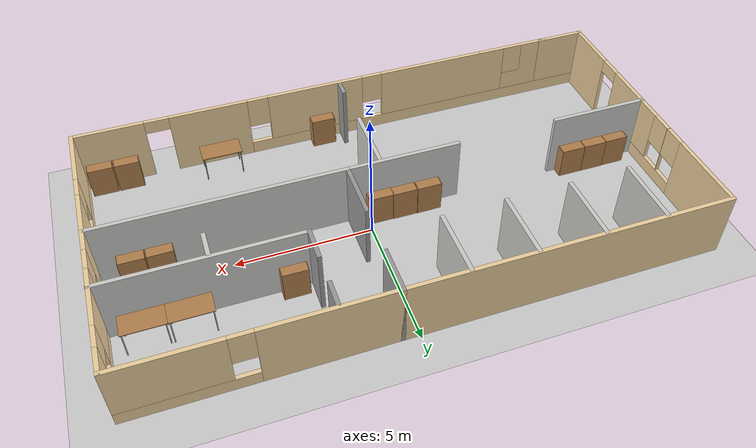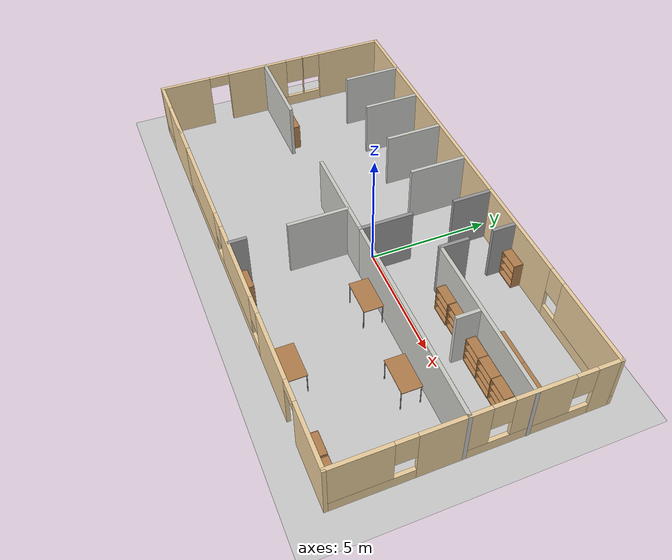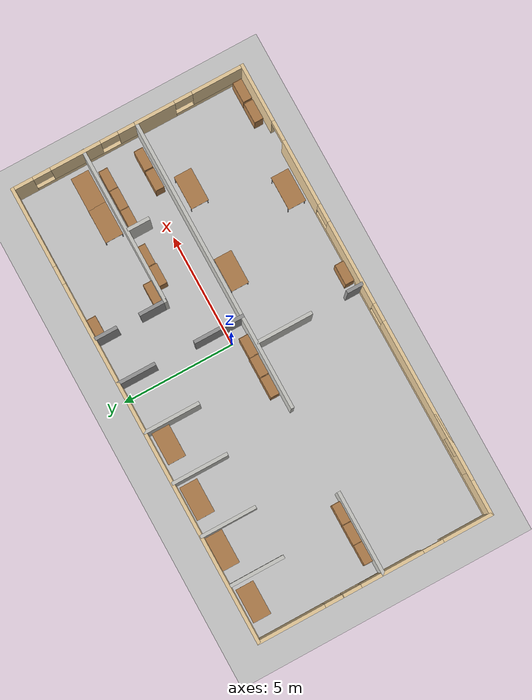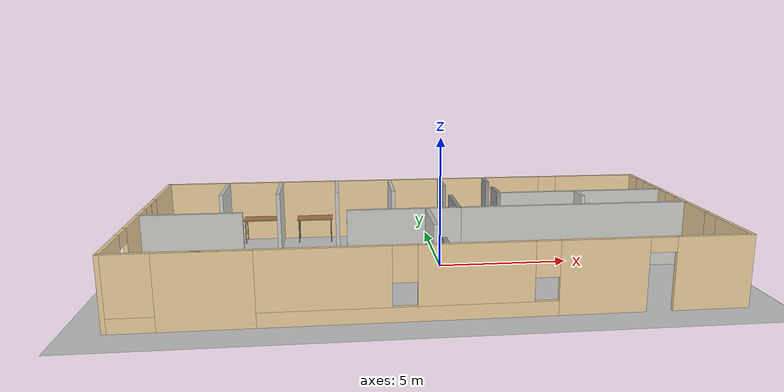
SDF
<sdf version="1.6">
 <world name="default">
  <light name="sun" type="directional">
   <pose>0 0 10 0 -0 0</pose>
   <diffuse>0.8 0.8 0.8 1</diffuse>
   <specular>0.2 0.2 0.2 1</specular>
   <attenuation>
    <range>1000</range>
    <constant>0.9</constant>
    <linear>0.01</linear>
    <quadratic>0.001</quadratic>
   </attenuation>
   <direction>-0.5 0.1 -0.9</direction>
  </light>
  <model name="ground_plane">
   <static>1</static>
   <link name="link">
    <collision name="collision">
     <geometry><plane><normal>0 0 1</normal><size>100 100</size></plane></geometry>
     <surface><friction><ode><mu>100</mu><mu2>50</mu2></ode></friction></surface>
    </collision>
    <visual name="visual">
     <cast_shadows>0</cast_shadows>
     <geometry><plane><normal>0 0 1</normal><size>100 100</size></plane></geometry>
     <material>
      <script><uri>file://media/materials/scripts/gazebo.material</uri><name>Gazebo/Grey</name></script>
     </material>
    </visual>
   </link>
  </model>
  <gravity>0 0 -9.8</gravity>
  <magnetic_field>6e-06 2.3e-05 -4.2e-05</magnetic_field>
  <atmosphere type="adiabatic"/>
  <physics name="default_physics" default="0" type="ode">
   <max_step_size>0.001</max_step_size>
   <real_time_factor>1</real_time_factor>
   <real_time_update_rate>1000</real_time_update_rate>
  </physics>
  <scene><ambient>0.4 0.4 0.4 1</ambient><background>0.7 0.7 0.7 1</background><shadows>1</shadows></scene>
  <audio><device>default</device></audio>
  <spherical_coordinates>
   <surface_model>EARTH_WGS84</surface_model>
   <latitude_deg>0</latitude_deg>
   <longitude_deg>0</longitude_deg>
   <elevation>0</elevation>
   <heading_deg>0</heading_deg>
  </spherical_coordinates>
  <model name="Office">
   <pose>-0.777206 -0.422928 0 0 -0 0</pose>
   <link name="Wall_10">
    <collision name="Wall_10_Collision">
     <geometry><box><size>2.25 0.15 2.5</size></box></geometry>
     <pose>0 0 1.25 0 -0 0</pose>
    </collision>
    <visual name="Wall_10_Visual">
     <pose>0 0 1.25 0 -0 0</pose>
     <geometry><box><size>2.25 0.15 2.5</size></box></geometry>
     <material>
      <script><uri>file://media/materials/scripts/gazebo.material</uri><name>Gazebo/Grey</name></script>
      <ambient>1 1 1 1</ambient>
     </material>
     <meta><layer>0</layer></meta>
    </visual>
    <pose>1.36821 0.675 0 0 -0 1.5708</pose>
   </link>
   <link name="Wall_12">
    <collision name="Wall_12_Collision">
     <geometry><box><size>1.75 0.15 2.5</size></box></geometry>
     <pose>0 0 1.25 0 -0 0</pose>
    </collision>
    <visual name="Wall_12_Visual">
     <pose>0 0 1.25 0 -0 0</pose>
     <geometry><box><size>1.75 0.15 2.5</size></box></geometry>
     <material>
      <script><uri>file://media/materials/scripts/gazebo.material</uri><name>Gazebo/Grey</name></script>
      <ambient>1 1 1 1</ambient>
     </material>
     <meta><layer>0</layer></meta>
    </visual>
    <pose>1.36821 4.425 0 0 -0 -1.5708</pose>
   </link>
   <link name="Wall_14">
    <collision name="Wall_14_Collision">
     <geometry><box><size>11.75 0.15 2.5</size></box></geometry>
     <pose>0 0 1.25 0 -0 0</pose>
    </collision>
    <visual name="Wall_14_Visual">
     <pose>0 0 1.25 0 -0 0</pose>
     <geometry><box><size>11.75 0.15 2.5</size></box></geometry>
     <material>
      <script><uri>file://media/materials/scripts/gazebo.material</uri><name>Gazebo/Grey</name></script>
      <ambient>0.921569 0.807843 0.615686 1</ambient>
     </material>
     <meta><layer>0</layer></meta>
    </visual>
    <pose>-4.43179 5.225 0 0 -0 3.14159</pose>
   </link>
   <link name="Wall_15">
    <pose>-10.2318 2.425 0 0 -0 -1.5708</pose>
    <visual name="Wall_15_Visual_0">
     <pose>-1.35159 0 1.25 0 -0 0</pose>
     <geometry><box><size>3.04683 0.15 2.5</size></box></geometry>
     <material>
      <script><uri>file://media/materials/scripts/gazebo.material</uri><name>Gazebo/Grey</name></script>
      <ambient>0.921569 0.807843 0.615686 1</ambient>
     </material>
     <meta><layer>0</layer></meta>
    </visual>
    <collision name="Wall_15_Collision_0">
     <geometry><box><size>3.04683 0.15 2.5</size></box></geometry>
     <pose>-1.35159 0 1.25 0 -0 0</pose>
    </collision>
    <visual name="Wall_15_Visual_1">
     <pose>1.52341 0 0.25 0 -0 0</pose>
     <geometry><box><size>2.70317 0.15 0.5</size></box></geometry>
     <material>
      <script><uri>file://media/materials/scripts/gazebo.material</uri><name>Gazebo/Grey</name></script>
      <ambient>0.921569 0.807843 0.615686 1</ambient>
     </material>
     <meta><layer>0</layer></meta>
    </visual>
    <collision name="Wall_15_Collision_1">
     <geometry><box><size>2.70317 0.15 0.5</size></box></geometry>
     <pose>1.52341 0 0.25 0 -0 0</pose>
    </collision>
    <visual name="Wall_15_Visual_2">
     <pose>0.984343 0 1.5 0 -0 0</pose>
     <geometry><box><size>0.02503 0.15 2</size></box></geometry>
     <material>
      <script><uri>file://media/materials/scripts/gazebo.material</uri><name>Gazebo/Grey</name></script>
      <ambient>0.921569 0.807843 0.615686 1</ambient>
     </material>
     <meta><layer>0</layer></meta>
    </visual>
    <collision name="Wall_15_Collision_2">
     <geometry><box><size>0.02503 0.15 2</size></box></geometry>
     <pose>0.984343 0 1.5 0 -0 0</pose>
    </collision>
    <visual name="Wall_15_Visual_3">
     <pose>2.33593 0 1.5 0 -0 0</pose>
     <geometry><box><size>1.07814 0.15 2</size></box></geometry>
     <material>
      <script><uri>file://media/materials/scripts/gazebo.material</uri><name>Gazebo/Grey</name></script>
      <ambient>0.921569 0.807843 0.615686 1</ambient>
     </material>
     <meta><layer>0</layer></meta>
    </visual>
    <collision name="Wall_15_Collision_3">
     <geometry><box><size>1.07814 0.15 2</size></box></geometry>
     <pose>2.33593 0 1.5 0 -0 0</pose>
    </collision>
    <visual name="Wall_15_Visual_4">
     <pose>0.571828 0 1.9 0 -0 0</pose>
     <geometry><box><size>0.8 0.15 1.2</size></box></geometry>
     <material>
      <script><uri>file://media/materials/scripts/gazebo.material</uri><name>Gazebo/Grey</name></script>
      <ambient>0.921569 0.807843 0.615686 1</ambient>
     </material>
     <meta><layer>0</layer></meta>
    </visual>
    <collision name="Wall_15_Collision_4">
     <geometry><box><size>0.8 0.15 1.2</size></box></geometry>
     <pose>0.571828 0 1.9 0 -0 0</pose>
    </collision>
    <visual name="Wall_15_Visual_5">
     <pose>1.39686 0 1.9 0 -0 0</pose>
     <geometry><box><size>0.8 0.15 1.2</size></box></geometry>
     <material>
      <script><uri>file://media/materials/scripts/gazebo.material</uri><name>Gazebo/Grey</name></script>
      <ambient>0.921569 0.807843 0.615686 1</ambient>
     </material>
     <meta><layer>0</layer></meta>
    </visual>
    <collision name="Wall_15_Collision_5">
     <geometry><box><size>0.8 0.15 1.2</size></box></geometry>
     <pose>1.39686 0 1.9 0 -0 0</pose>
    </collision>
   </link>
   <link name="Wall_19">
    <collision name="Wall_19_Collision">
     <geometry><box><size>2.5 0.15 2.5</size></box></geometry>
     <pose>0 0 1.25 0 -0 0</pose>
    </collision>
    <visual name="Wall_19_Visual">
     <pose>0 0 1.25 0 -0 0</pose>
     <geometry><box><size>2.5 0.15 2.5</size></box></geometry>
     <material>
      <script><uri>file://media/materials/scripts/gazebo.material</uri><name>Gazebo/CeilingTiled</name></script>
      <ambient>1 1 1 1</ambient>
     </material>
     <meta><layer>0</layer></meta>
    </visual>
    <pose>-7.76288 3.97866 0 0 -0 -1.5708</pose>
   </link>
   <link name="Wall_23">
    <collision name="Wall_23_Collision">
     <geometry><box><size>2.5 0.15 2.5</size></box></geometry>
     <pose>0 0 1.25 0 -0 0</pose>
    </collision>
    <visual name="Wall_23_Visual">
     <pose>0 0 1.25 0 -0 0</pose>
     <geometry><box><size>2.5 0.15 2.5</size></box></geometry>
     <material>
      <script><uri>file://media/materials/scripts/gazebo.material</uri><name>Gazebo/CeilingTiled</name></script>
      <ambient>1 1 1 1</ambient>
     </material>
     <meta><layer>0</layer></meta>
    </visual>
    <pose>-5.51578 4.01433 0 0 -0 -1.5708</pose>
   </link>
   <link name="Wall_25">
    <collision name="Wall_25_Collision">
     <geometry><box><size>2.5 0.15 2.5</size></box></geometry>
     <pose>0 0 1.25 0 -0 0</pose>
    </collision>
    <visual name="Wall_25_Visual">
     <pose>0 0 1.25 0 -0 0</pose>
     <geometry><box><size>2.5 0.15 2.5</size></box></geometry>
     <material>
      <script><uri>file://media/materials/scripts/gazebo.material</uri><name>Gazebo/CeilingTiled</name></script>
      <ambient>1 1 1 1</ambient>
     </material>
     <meta><layer>0</layer></meta>
    </visual>
    <pose>-3.14383 3.9965 0 0 -0 -1.5708</pose>
   </link>
   <link name="Wall_29">
    <collision name="Wall_29_Collision">
     <geometry><box><size>2.5 0.15 2.5</size></box></geometry>
     <pose>0 0 1.25 0 -0 0</pose>
    </collision>
    <visual name="Wall_29_Visual">
     <pose>0 0 1.25 0 -0 0</pose>
     <geometry><box><size>2.5 0.15 2.5</size></box></geometry>
     <material>
      <script><uri>file://media/materials/scripts/gazebo.material</uri><name>Gazebo/CeilingTiled</name></script>
      <ambient>1 1 1 1</ambient>
     </material>
     <meta><layer>0</layer></meta>
    </visual>
    <pose>-0.843227 4.01433 0 0 -0 -1.5708</pose>
   </link>
   <link name="Wall_39">
    <collision name="Wall_39_Collision">
     <geometry><box><size>7 0.15 2.5</size></box></geometry>
     <pose>0 0 1.25 0 -0 0</pose>
    </collision>
    <visual name="Wall_39_Visual">
     <pose>0 0 1.25 0 -0 0</pose>
     <geometry><box><size>7 0.15 2.5</size></box></geometry>
     <material>
      <script><uri>file://media/materials/scripts/gazebo.material</uri><name>Gazebo/CeilingTiled</name></script>
      <ambient>1 1 1 1</ambient>
     </material>
     <meta><layer>0</layer></meta>
    </visual>
    <pose>6.80679 2.01485 0 0 -0 3.14159</pose>
   </link>
   <link name="Wall_40">
    <collision name="Wall_40_Collision">
     <geometry><box><size>1.25 0.15 2.5</size></box></geometry>
     <pose>0 0 1.25 0 -0 0</pose>
    </collision>
    <visual name="Wall_40_Visual">
     <pose>0 0 1.25 0 -0 0</pose>
     <geometry><box><size>1.25 0.15 2.5</size></box></geometry>
     <material>
      <script><uri>file://media/materials/scripts/gazebo.material</uri><name>Gazebo/Grey</name></script>
      <ambient>1 1 1 1</ambient>
     </material>
     <meta><layer>0</layer></meta>
    </visual>
    <pose>3.38179 2.56485 0 0 -0 1.5708</pose>
   </link>
   <link name="Wall_43">
    <collision name="Wall_43_Collision">
     <geometry><box><size>1 0.15 2.5</size></box></geometry>
     <pose>0 0 1.25 0 -0 0</pose>
    </collision>
    <visual name="Wall_43_Visual">
     <pose>0 0 1.25 0 -0 0</pose>
     <geometry><box><size>1 0.15 2.5</size></box></geometry>
     <material>
      <script><uri>file://media/materials/scripts/gazebo.material</uri><name>Gazebo/Grey</name></script>
      <ambient>1 1 1 1</ambient>
     </material>
     <meta><layer>0</layer></meta>
    </visual>
    <pose>3.36564 4.69299 0 0 -0 -1.5708</pose>
   </link>
   <link name="Wall_45">
    <collision name="Wall_45_Collision">
     <geometry><box><size>1 0.15 2.5</size></box></geometry>
     <pose>0 0 1.25 0 -0 0</pose>
    </collision>
    <visual name="Wall_45_Visual">
     <pose>0 0 1.25 0 -0 0</pose>
     <geometry><box><size>1 0.15 2.5</size></box></geometry>
     <material>
      <script><uri>file://media/materials/scripts/gazebo.material</uri><name>Gazebo/CeilingTiled</name></script>
      <ambient>1 1 1 1</ambient>
     </material>
     <meta><layer>0</layer></meta>
    </visual>
    <pose>6.59362 1.48284 0 0 -0 -1.5708</pose>
   </link>
   <link name="Wall_47">
    <collision name="Wall_47_Collision">
     <geometry><box><size>3.75 0.15 2.5</size></box></geometry>
     <pose>0 0 1.25 0 -0 0</pose>
    </collision>
    <visual name="Wall_47_Visual">
     <pose>0 0 1.25 0 -0 0</pose>
     <geometry><box><size>3.75 0.15 2.5</size></box></geometry>
     <material>
      <script><uri>file://media/materials/scripts/gazebo.material</uri><name>Gazebo/CeilingTiled</name></script>
      <ambient>1 1 1 1</ambient>
     </material>
     <meta><layer>0</layer></meta>
    </visual>
    <pose>-8.43179 -0.375 0 0 -0 0</pose>
   </link>
   <link name="Wall_51">
    <collision name="Wall_51_Collision">
     <geometry><box><size>4.25 0.15 2.5</size></box></geometry>
     <pose>0 0 1.25 0 -0 0</pose>
    </collision>
    <visual name="Wall_51_Visual">
     <pose>0 0 1.25 0 -0 0</pose>
     <geometry><box><size>4.25 0.15 2.5</size></box></geometry>
     <material>
      <script><uri>file://media/materials/scripts/gazebo.material</uri><name>Gazebo/CeilingTiled</name></script>
      <ambient>1 1 1 1</ambient>
     </material>
     <meta><layer>0</layer></meta>
    </visual>
    <pose>-0.68179 -0.375 0 0 -0 3.14159</pose>
   </link>
   <link name="Wall_53">
    <pose>-10.2318 -2.8 0 0 -0 -1.5708</pose>
    <visual name="Wall_53_Visual_0">
     <pose>-1.56713 0 1.25 0 -0 0</pose>
     <geometry><box><size>1.86574 0.15 2.5</size></box></geometry>
     <material>
      <script><uri>file://media/materials/scripts/gazebo.material</uri><name>Gazebo/Grey</name></script>
      <ambient>0.921569 0.807843 0.615686 1</ambient>
     </material>
     <meta><layer>0</layer></meta>
    </visual>
    <collision name="Wall_53_Collision_0">
     <geometry><box><size>1.86574 0.15 2.5</size></box></geometry>
     <pose>-1.56713 0 1.25 0 -0 0</pose>
    </collision>
    <visual name="Wall_53_Visual_1">
     <pose>1.38287 0 1.25 0 -0 0</pose>
     <geometry><box><size>2.23426 0.15 2.5</size></box></geometry>
     <material>
      <script><uri>file://media/materials/scripts/gazebo.material</uri><name>Gazebo/Grey</name></script>
      <ambient>0.921569 0.807843 0.615686 1</ambient>
     </material>
     <meta><layer>0</layer></meta>
    </visual>
    <collision name="Wall_53_Collision_1">
     <geometry><box><size>2.23426 0.15 2.5</size></box></geometry>
     <pose>1.38287 0 1.25 0 -0 0</pose>
    </collision>
    <visual name="Wall_53_Visual_2">
     <pose>-0.184259 0 2.25 0 -0 0</pose>
     <geometry><box><size>0.9 0.15 0.5</size></box></geometry>
     <material>
      <script><uri>file://media/materials/scripts/gazebo.material</uri><name>Gazebo/Grey</name></script>
      <ambient>0.921569 0.807843 0.615686 1</ambient>
     </material>
     <meta><layer>0</layer></meta>
    </visual>
    <collision name="Wall_53_Collision_2">
     <geometry><box><size>0.9 0.15 0.5</size></box></geometry>
     <pose>-0.184259 0 2.25 0 -0 0</pose>
    </collision>
   </link>
   <link name="Wall_63">
    <pose>10.2182 -2.8 0 0 -0 -1.5708</pose>
    <visual name="Wall_63_Visual_0">
     <pose>-1.59369 0 1.25 0 -0 0</pose>
     <geometry><box><size>1.81261 0.15 2.5</size></box></geometry>
     <material>
      <script><uri>file://media/materials/scripts/gazebo.material</uri><name>Gazebo/Grey</name></script>
      <ambient>0.921569 0.807843 0.615686 1</ambient>
     </material>
     <meta><layer>0</layer></meta>
    </visual>
    <collision name="Wall_63_Collision_0">
     <geometry><box><size>1.81261 0.15 2.5</size></box></geometry>
     <pose>-1.59369 0 1.25 0 -0 0</pose>
    </collision>
    <visual name="Wall_63_Visual_1">
     <pose>0.906306 0 0.25 0 -0 0</pose>
     <geometry><box><size>3.18739 0.15 0.5</size></box></geometry>
     <material>
      <script><uri>file://media/materials/scripts/gazebo.material</uri><name>Gazebo/Grey</name></script>
      <ambient>0.921569 0.807843 0.615686 1</ambient>
     </material>
     <meta><layer>0</layer></meta>
    </visual>
    <collision name="Wall_63_Collision_1">
     <geometry><box><size>3.18739 0.15 0.5</size></box></geometry>
     <pose>0.906306 0 0.25 0 -0 0</pose>
    </collision>
    <visual name="Wall_63_Visual_2">
     <pose>1.30631 0 1.5 0 -0 0</pose>
     <geometry><box><size>2.38739 0.15 2</size></box></geometry>
     <material>
      <script><uri>file://media/materials/scripts/gazebo.material</uri><name>Gazebo/Grey</name></script>
      <ambient>0.921569 0.807843 0.615686 1</ambient>
     </material>
     <meta><layer>0</layer></meta>
    </visual>
    <collision name="Wall_63_Collision_2">
     <geometry><box><size>2.38739 0.15 2</size></box></geometry>
     <pose>1.30631 0 1.5 0 -0 0</pose>
    </collision>
    <visual name="Wall_63_Visual_3">
     <pose>-0.287388 0 1.9 0 -0 0</pose>
     <geometry><box><size>0.8 0.15 1.2</size></box></geometry>
     <material>
      <script><uri>file://media/materials/scripts/gazebo.material</uri><name>Gazebo/Grey</name></script>
      <ambient>0.921569 0.807843 0.615686 1</ambient>
     </material>
     <meta><layer>0</layer></meta>
    </visual>
    <collision name="Wall_63_Collision_3">
     <geometry><box><size>0.8 0.15 1.2</size></box></geometry>
     <pose>-0.287388 0 1.9 0 -0 0</pose>
    </collision>
   </link>
   <link name="Wall_64">
    <pose>-0.00679 -5.225 0 0 -0 3.14159</pose>
    <visual name="Wall_64_Visual_0">
     <pose>-8.98546 0 1.25 0 -0 0</pose>
     <geometry><box><size>2.62907 0.15 2.5</size></box></geometry>
     <material>
      <script><uri>file://media/materials/scripts/gazebo.material</uri><name>Gazebo/Grey</name></script>
      <ambient>0.921569 0.807843 0.615686 1</ambient>
     </material>
     <meta><layer>0</layer></meta>
    </visual>
    <collision name="Wall_64_Collision_0">
     <geometry><box><size>2.62907 0.15 2.5</size></box></geometry>
     <pose>-8.98546 0 1.25 0 -0 0</pose>
    </collision>
    <visual name="Wall_64_Visual_1">
     <pose>-5.30524 0 1.25 0 -0 0</pose>
     <geometry><box><size>2.93139 0.15 2.5</size></box></geometry>
     <material>
      <script><uri>file://media/materials/scripts/gazebo.material</uri><name>Gazebo/Grey</name></script>
      <ambient>0.921569 0.807843 0.615686 1</ambient>
     </material>
     <meta><layer>0</layer></meta>
    </visual>
    <collision name="Wall_64_Collision_1">
     <geometry><box><size>2.93139 0.15 2.5</size></box></geometry>
     <pose>-5.30524 0 1.25 0 -0 0</pose>
    </collision>
    <visual name="Wall_64_Visual_2">
     <pose>3.23023 0 0.25 0 -0 0</pose>
     <geometry><box><size>14.1395 0.15 0.5</size></box></geometry>
     <material>
      <script><uri>file://media/materials/scripts/gazebo.material</uri><name>Gazebo/Grey</name></script>
      <ambient>0.921569 0.807843 0.615686 1</ambient>
     </material>
     <meta><layer>0</layer></meta>
    </visual>
    <collision name="Wall_64_Collision_2">
     <geometry><box><size>14.1395 0.15 0.5</size></box></geometry>
     <pose>3.23023 0 0.25 0 -0 0</pose>
    </collision>
    <visual name="Wall_64_Visual_3">
     <pose>-1.17071 0 1.5 0 -0 0</pose>
     <geometry><box><size>3.73767 0.15 2</size></box></geometry>
     <material>
      <script><uri>file://media/materials/scripts/gazebo.material</uri><name>Gazebo/Grey</name></script>
      <ambient>0.921569 0.807843 0.615686 1</ambient>
     </material>
     <meta><layer>0</layer></meta>
    </visual>
    <collision name="Wall_64_Collision_3">
     <geometry><box><size>3.73767 0.15 2</size></box></geometry>
     <pose>-1.17071 0 1.5 0 -0 0</pose>
    </collision>
    <visual name="Wall_64_Visual_4">
     <pose>4.12324 0 1.5 0 -0 0</pose>
     <geometry><box><size>5.25022 0.15 2</size></box></geometry>
     <material>
      <script><uri>file://media/materials/scripts/gazebo.material</uri><name>Gazebo/Grey</name></script>
      <ambient>0.921569 0.807843 0.615686 1</ambient>
     </material>
     <meta><layer>0</layer></meta>
    </visual>
    <collision name="Wall_64_Collision_4">
     <geometry><box><size>5.25022 0.15 2</size></box></geometry>
     <pose>4.12324 0 1.5 0 -0 0</pose>
    </collision>
    <visual name="Wall_64_Visual_5">
     <pose>9.3195 0 1.5 0 -0 0</pose>
     <geometry><box><size>1.961 0.15 2</size></box></geometry>
     <material>
      <script><uri>file://media/materials/scripts/gazebo.material</uri><name>Gazebo/Grey</name></script>
      <ambient>0.921569 0.807843 0.615686 1</ambient>
     </material>
     <meta><layer>0</layer></meta>
    </visual>
    <collision name="Wall_64_Collision_5">
     <geometry><box><size>1.961 0.15 2</size></box></geometry>
     <pose>9.3195 0 1.5 0 -0 0</pose>
    </collision>
    <visual name="Wall_64_Visual_6">
     <pose>-3.43954 0 1.9 0 -0 0</pose>
     <geometry><box><size>0.8 0.15 1.2</size></box></geometry>
     <material>
      <script><uri>file://media/materials/scripts/gazebo.material</uri><name>Gazebo/Grey</name></script>
      <ambient>0.921569 0.807843 0.615686 1</ambient>
     </material>
     <meta><layer>0</layer></meta>
    </visual>
    <collision name="Wall_64_Collision_6">
     <geometry><box><size>0.8 0.15 1.2</size></box></geometry>
     <pose>-3.43954 0 1.9 0 -0 0</pose>
    </collision>
    <visual name="Wall_64_Visual_7">
     <pose>1.09813 0 1.9 0 -0 0</pose>
     <geometry><box><size>0.8 0.15 1.2</size></box></geometry>
     <material>
      <script><uri>file://media/materials/scripts/gazebo.material</uri><name>Gazebo/Grey</name></script>
      <ambient>0.921569 0.807843 0.615686 1</ambient>
     </material>
     <meta><layer>0</layer></meta>
    </visual>
    <collision name="Wall_64_Collision_7">
     <geometry><box><size>0.8 0.15 1.2</size></box></geometry>
     <pose>1.09813 0 1.9 0 -0 0</pose>
    </collision>
    <visual name="Wall_64_Visual_8">
     <pose>7.14367 0 1.9 0 -0 0</pose>
     <geometry><box><size>0.790654 0.15 1.2</size></box></geometry>
     <material>
      <script><uri>file://media/materials/scripts/gazebo.material</uri><name>Gazebo/Grey</name></script>
      <ambient>0.921569 0.807843 0.615686 1</ambient>
     </material>
     <meta><layer>0</layer></meta>
    </visual>
    <collision name="Wall_64_Collision_8">
     <geometry><box><size>0.790654 0.15 1.2</size></box></geometry>
     <pose>7.14367 0 1.9 0 -0 0</pose>
    </collision>
    <visual name="Wall_64_Visual_9">
     <pose>-7.22093 0 2.25 0 -0 0</pose>
     <geometry><box><size>0.9 0.15 0.5</size></box></geometry>
     <material>
      <script><uri>file://media/materials/scripts/gazebo.material</uri><name>Gazebo/Grey</name></script>
      <ambient>0.921569 0.807843 0.615686 1</ambient>
     </material>
     <meta><layer>0</layer></meta>
    </visual>
    <collision name="Wall_64_Collision_9">
     <geometry><box><size>0.9 0.15 0.5</size></box></geometry>
     <pose>-7.22093 0 2.25 0 -0 0</pose>
    </collision>
   </link>
   <link name="Wall_66">
    <collision name="Wall_66_Collision">
     <geometry><box><size>2.5 0.15 2.5</size></box></geometry>
     <pose>0 0 1.25 0 -0 0</pose>
    </collision>
    <visual name="Wall_66_Visual">
     <pose>0 0 1.25 0 -0 0</pose>
     <geometry><box><size>2.5 0.15 2.5</size></box></geometry>
     <material>
      <script><uri>file://media/materials/scripts/gazebo.material</uri><name>Gazebo/CeilingTiled</name></script>
      <ambient>1 1 1 1</ambient>
     </material>
     <meta><layer>0</layer></meta>
    </visual>
    <pose>0.166381 -1.63332 0 0 -0 -1.5708</pose>
   </link>
   <link name="Wall_68">
    <collision name="Wall_68_Collision">
     <geometry><box><size>0.75 0.15 2.5</size></box></geometry>
     <pose>0 0 1.25 0 -0 0</pose>
    </collision>
    <visual name="Wall_68_Visual">
     <pose>0 0 1.25 0 -0 0</pose>
     <geometry><box><size>0.75 0.15 2.5</size></box></geometry>
     <material>
      <script><uri>file://media/materials/scripts/gazebo.material</uri><name>Gazebo/Grey</name></script>
      <ambient>1 1 1 1</ambient>
     </material>
     <meta><layer>0</layer></meta>
    </visual>
    <pose>0.217654 -4.86018 0 0 -0 -1.5708</pose>
   </link>
   <link name="Wall_7">
    <pose>5.79321 5.225 0 0 -0 0</pose>
    <visual name="Wall_7_Visual_0">
     <pose>-2.20361 0 1.25 0 -0 0</pose>
     <geometry><box><size>4.59277 0.15 2.5</size></box></geometry>
     <material>
      <script><uri>file://media/materials/scripts/gazebo.material</uri><name>Gazebo/Grey</name></script>
      <ambient>0.921569 0.807843 0.615686 1</ambient>
     </material>
     <meta><layer>0</layer></meta>
    </visual>
    <collision name="Wall_7_Collision_0">
     <geometry><box><size>4.59277 0.15 2.5</size></box></geometry>
     <pose>-2.20361 0 1.25 0 -0 0</pose>
    </collision>
    <visual name="Wall_7_Visual_1">
     <pose>2.29639 0 0.25 0 -0 0</pose>
     <geometry><box><size>4.40723 0.15 0.5</size></box></geometry>
     <material>
      <script><uri>file://media/materials/scripts/gazebo.material</uri><name>Gazebo/Grey</name></script>
      <ambient>0.921569 0.807843 0.615686 1</ambient>
     </material>
     <meta><layer>0</layer></meta>
    </visual>
    <collision name="Wall_7_Collision_1">
     <geometry><box><size>4.40723 0.15 0.5</size></box></geometry>
     <pose>2.29639 0 0.25 0 -0 0</pose>
    </collision>
    <visual name="Wall_7_Visual_2">
     <pose>2.69639 0 1.5 0 -0 0</pose>
     <geometry><box><size>3.60723 0.15 2</size></box></geometry>
     <material>
      <script><uri>file://media/materials/scripts/gazebo.material</uri><name>Gazebo/Grey</name></script>
      <ambient>0.921569 0.807843 0.615686 1</ambient>
     </material>
     <meta><layer>0</layer></meta>
    </visual>
    <collision name="Wall_7_Collision_2">
     <geometry><box><size>3.60723 0.15 2</size></box></geometry>
     <pose>2.69639 0 1.5 0 -0 0</pose>
    </collision>
    <visual name="Wall_7_Visual_3">
     <pose>0.492771 0 1.9 0 -0 0</pose>
     <geometry><box><size>0.8 0.15 1.2</size></box></geometry>
     <material>
      <script><uri>file://media/materials/scripts/gazebo.material</uri><name>Gazebo/Grey</name></script>
      <ambient>0.921569 0.807843 0.615686 1</ambient>
     </material>
     <meta><layer>0</layer></meta>
    </visual>
    <collision name="Wall_7_Collision_3">
     <geometry><box><size>0.8 0.15 1.2</size></box></geometry>
     <pose>0.492771 0 1.9 0 -0 0</pose>
    </collision>
   </link>
   <link name="Wall_8">
    <pose>10.2182 2.425 0 0 -0 -1.5708</pose>
    <visual name="Wall_8_Visual_0">
     <pose>-2.38287 0 1.25 0 -0 0</pose>
     <geometry><box><size>0.984252 0.15 2.5</size></box></geometry>
     <material>
      <script><uri>file://media/materials/scripts/gazebo.material</uri><name>Gazebo/Grey</name></script>
      <ambient>0.921569 0.807843 0.615686 1</ambient>
     </material>
     <meta><layer>0</layer></meta>
    </visual>
    <collision name="Wall_8_Collision_0">
     <geometry><box><size>0.984252 0.15 2.5</size></box></geometry>
     <pose>-2.38287 0 1.25 0 -0 0</pose>
    </collision>
    <visual name="Wall_8_Visual_1">
     <pose>0.492126 0 0.25 0 -0 0</pose>
     <geometry><box><size>4.76575 0.15 0.5</size></box></geometry>
     <material>
      <script><uri>file://media/materials/scripts/gazebo.material</uri><name>Gazebo/Grey</name></script>
      <ambient>0.921569 0.807843 0.615686 1</ambient>
     </material>
     <meta><layer>0</layer></meta>
    </visual>
    <collision name="Wall_8_Collision_1">
     <geometry><box><size>4.76575 0.15 0.5</size></box></geometry>
     <pose>0.492126 0 0.25 0 -0 0</pose>
    </collision>
    <visual name="Wall_8_Visual_2">
     <pose>0.038996 0 1.5 0 -0 0</pose>
     <geometry><box><size>2.25949 0.15 2</size></box></geometry>
     <material>
      <script><uri>file://media/materials/scripts/gazebo.material</uri><name>Gazebo/Grey</name></script>
      <ambient>0.921569 0.807843 0.615686 1</ambient>
     </material>
     <meta><layer>0</layer></meta>
    </visual>
    <collision name="Wall_8_Collision_2">
     <geometry><box><size>2.25949 0.15 2</size></box></geometry>
     <pose>0.038996 0 1.5 0 -0 0</pose>
    </collision>
    <visual name="Wall_8_Visual_3">
     <pose>2.42187 0 1.5 0 -0 0</pose>
     <geometry><box><size>0.906261 0.15 2</size></box></geometry>
     <material>
      <script><uri>file://media/materials/scripts/gazebo.material</uri><name>Gazebo/Grey</name></script>
      <ambient>0.921569 0.807843 0.615686 1</ambient>
     </material>
     <meta><layer>0</layer></meta>
    </visual>
    <collision name="Wall_8_Collision_3">
     <geometry><box><size>0.906261 0.15 2</size></box></geometry>
     <pose>2.42187 0 1.5 0 -0 0</pose>
    </collision>
    <visual name="Wall_8_Visual_4">
     <pose>-1.49075 0 1.9 0 -0 0</pose>
     <geometry><box><size>0.8 0.15 1.2</size></box></geometry>
     <material>
      <script><uri>file://media/materials/scripts/gazebo.material</uri><name>Gazebo/Grey</name></script>
      <ambient>0.921569 0.807843 0.615686 1</ambient>
     </material>
     <meta><layer>0</layer></meta>
    </visual>
    <collision name="Wall_8_Collision_4">
     <geometry><box><size>0.8 0.15 1.2</size></box></geometry>
     <pose>-1.49075 0 1.9 0 -0 0</pose>
    </collision>
    <visual name="Wall_8_Visual_5">
     <pose>1.56874 0 1.9 0 -0 0</pose>
     <geometry><box><size>0.8 0.15 1.2</size></box></geometry>
     <material>
      <script><uri>file://media/materials/scripts/gazebo.material</uri><name>Gazebo/Grey</name></script>
      <ambient>0.921569 0.807843 0.615686 1</ambient>
     </material>
     <meta><layer>0</layer></meta>
    </visual>
    <collision name="Wall_8_Collision_5">
     <geometry><box><size>0.8 0.15 1.2</size></box></geometry>
     <pose>1.56874 0 1.9 0 -0 0</pose>
    </collision>
   </link>
   <link name="Wall_9">
    <collision name="Wall_9_Collision">
     <geometry><box><size>9 0.15 2.5</size></box></geometry>
     <pose>0 0 1.25 0 -0 0</pose>
    </collision>
    <visual name="Wall_9_Visual">
     <pose>0 0 1.25 0 -0 0</pose>
     <geometry><box><size>9 0.15 2.5</size></box></geometry>
     <material>
      <script><uri>file://media/materials/scripts/gazebo.material</uri><name>Gazebo/CeilingTiled</name></script>
      <ambient>1 1 1 1</ambient>
     </material>
     <meta><layer>0</layer></meta>
    </visual>
    <pose>5.79321 -0.375 0 0 -0 3.14159</pose>
   </link>
   <static>1</static>
  </model>
  <model name="Office1">
   <pose>-7.98552 -5.65127 0 0 -0 0</pose>
   <link name="Wall_85">
    <collision name="Wall_85_Collision">
     <geometry><box><size>3 0.15 2.5</size></box></geometry>
     <pose>0 0 1.25 0 -0 0</pose>
    </collision>
    <visual name="Wall_85_Visual">
     <pose>0 0 1.25 0 -0 0</pose>
     <geometry><box><size>3 0.15 2.5</size></box></geometry>
     <material>
      <script><uri>file://media/materials/scripts/gazebo.material</uri><name>Gazebo/Grey</name></script>
      <ambient>0.921569 0.807843 0.615686 1</ambient>
     </material>
     <meta><layer>0</layer></meta>
    </visual>
   </link>
   <static>1</static>
  </model>
  <model name="table">
   <static>1</static>
   <link name="link">
    <collision name="surface">
     <pose>0 0 1 0 -0 0</pose>
     <geometry><box><size>1.5 0.8 0.03</size></box></geometry>
     <surface><friction><ode><mu>0.6</mu><mu2>0.6</mu2></ode></friction></surface>
    </collision>
    <visual name="visual1">
     <pose>0 0 1 0 -0 0</pose>
     <geometry><box><size>1.5 0.8 0.03</size></box></geometry>
     <material>
      <script><uri>file://media/materials/scripts/gazebo.material</uri><name>Gazebo/Wood</name></script>
     </material>
    </visual>
    <collision name="front_left_leg">
     <pose>0.68 0.38 0.5 0 -0 0</pose>
     <geometry><cylinder><radius>0.02</radius><length>1</length></cylinder></geometry>
    </collision>
    <visual name="front_left_leg">
     <pose>0.68 0.38 0.5 0 -0 0</pose>
     <geometry><cylinder><radius>0.02</radius><length>1</length></cylinder></geometry>
     <material>
      <script><uri>file://media/materials/scripts/gazebo.material</uri><name>Gazebo/Grey</name></script>
     </material>
    </visual>
    <collision name="front_right_leg">
     <pose>0.68 -0.38 0.5 0 -0 0</pose>
     <geometry><cylinder><radius>0.02</radius><length>1</length></cylinder></geometry>
    </collision>
    <visual name="front_right_leg">
     <pose>0.68 -0.38 0.5 0 -0 0</pose>
     <geometry><cylinder><radius>0.02</radius><length>1</length></cylinder></geometry>
     <material>
      <script><uri>file://media/materials/scripts/gazebo.material</uri><name>Gazebo/Grey</name></script>
     </material>
    </visual>
    <collision name="back_right_leg">
     <pose>-0.68 -0.38 0.5 0 -0 0</pose>
     <geometry><cylinder><radius>0.02</radius><length>1</length></cylinder></geometry>
    </collision>
    <visual name="back_right_leg">
     <pose>-0.68 -0.38 0.5 0 -0 0</pose>
     <geometry><cylinder><radius>0.02</radius><length>1</length></cylinder></geometry>
     <material>
      <script><uri>file://media/materials/scripts/gazebo.material</uri><name>Gazebo/Grey</name></script>
     </material>
    </visual>
    <collision name="back_left_leg">
     <pose>-0.68 0.38 0.5 0 -0 0</pose>
     <geometry><cylinder><radius>0.02</radius><length>1</length></cylinder></geometry>
    </collision>
    <visual name="back_left_leg">
     <pose>-0.68 0.38 0.5 0 -0 0</pose>
     <geometry><cylinder><radius>0.02</radius><length>1</length></cylinder></geometry>
     <material>
      <script><uri>file://media/materials/scripts/gazebo.material</uri><name>Gazebo/Grey</name></script>
     </material>
    </visual>
   </link>
   <pose>-2.37431 4.20613 0 0 -0 0</pose>
  </model>
  <model name="table_0">
   <static>1</static>
   <link name="link">
    <collision name="surface">
     <pose>0 0 1 0 -0 0</pose>
     <geometry><box><size>1.5 0.8 0.03</size></box></geometry>
     <surface><friction><ode><mu>0.6</mu><mu2>0.6</mu2></ode></friction></surface>
    </collision>
    <visual name="visual1">
     <pose>0 0 1 0 -0 0</pose>
     <geometry><box><size>1.5 0.8 0.03</size></box></geometry>
     <material>
      <script><uri>file://media/materials/scripts/gazebo.material</uri><name>Gazebo/Wood</name></script>
     </material>
    </visual>
    <collision name="front_left_leg">
     <pose>0.68 0.38 0.5 0 -0 0</pose>
     <geometry><cylinder><radius>0.02</radius><length>1</length></cylinder></geometry>
    </collision>
    <visual name="front_left_leg">
     <pose>0.68 0.38 0.5 0 -0 0</pose>
     <geometry><cylinder><radius>0.02</radius><length>1</length></cylinder></geometry>
     <material>
      <script><uri>file://media/materials/scripts/gazebo.material</uri><name>Gazebo/Grey</name></script>
     </material>
    </visual>
    <collision name="front_right_leg">
     <pose>0.68 -0.38 0.5 0 -0 0</pose>
     <geometry><cylinder><radius>0.02</radius><length>1</length></cylinder></geometry>
    </collision>
    <visual name="front_right_leg">
     <pose>0.68 -0.38 0.5 0 -0 0</pose>
     <geometry><cylinder><radius>0.02</radius><length>1</length></cylinder></geometry>
     <material>
      <script><uri>file://media/materials/scripts/gazebo.material</uri><name>Gazebo/Grey</name></script>
     </material>
    </visual>
    <collision name="back_right_leg">
     <pose>-0.68 -0.38 0.5 0 -0 0</pose>
     <geometry><cylinder><radius>0.02</radius><length>1</length></cylinder></geometry>
    </collision>
    <visual name="back_right_leg">
     <pose>-0.68 -0.38 0.5 0 -0 0</pose>
     <geometry><cylinder><radius>0.02</radius><length>1</length></cylinder></geometry>
     <material>
      <script><uri>file://media/materials/scripts/gazebo.material</uri><name>Gazebo/Grey</name></script>
     </material>
    </visual>
    <collision name="back_left_leg">
     <pose>-0.68 0.38 0.5 0 -0 0</pose>
     <geometry><cylinder><radius>0.02</radius><length>1</length></cylinder></geometry>
    </collision>
    <visual name="back_left_leg">
     <pose>-0.68 0.38 0.5 0 -0 0</pose>
     <geometry><cylinder><radius>0.02</radius><length>1</length></cylinder></geometry>
     <material>
      <script><uri>file://media/materials/scripts/gazebo.material</uri><name>Gazebo/Grey</name></script>
     </material>
    </visual>
   </link>
   <pose>-4.88669 4.25814 0 0 -0 0</pose>
  </model>
  <model name="table_1">
   <static>1</static>
   <link name="link">
    <collision name="surface">
     <pose>0 0 1 0 -0 0</pose>
     <geometry><box><size>1.5 0.8 0.03</size></box></geometry>
     <surface><friction><ode><mu>0.6</mu><mu2>0.6</mu2></ode></friction></surface>
    </collision>
    <visual name="visual1">
     <pose>0 0 1 0 -0 0</pose>
     <geometry><box><size>1.5 0.8 0.03</size></box></geometry>
     <material>
      <script><uri>file://media/materials/scripts/gazebo.material</uri><name>Gazebo/Wood</name></script>
     </material>
    </visual>
    <collision name="front_left_leg">
     <pose>0.68 0.38 0.5 0 -0 0</pose>
     <geometry><cylinder><radius>0.02</radius><length>1</length></cylinder></geometry>
    </collision>
    <visual name="front_left_leg">
     <pose>0.68 0.38 0.5 0 -0 0</pose>
     <geometry><cylinder><radius>0.02</radius><length>1</length></cylinder></geometry>
     <material>
      <script><uri>file://media/materials/scripts/gazebo.material</uri><name>Gazebo/Grey</name></script>
     </material>
    </visual>
    <collision name="front_right_leg">
     <pose>0.68 -0.38 0.5 0 -0 0</pose>
     <geometry><cylinder><radius>0.02</radius><length>1</length></cylinder></geometry>
    </collision>
    <visual name="front_right_leg">
     <pose>0.68 -0.38 0.5 0 -0 0</pose>
     <geometry><cylinder><radius>0.02</radius><length>1</length></cylinder></geometry>
     <material>
      <script><uri>file://media/materials/scripts/gazebo.material</uri><name>Gazebo/Grey</name></script>
     </material>
    </visual>
    <collision name="back_right_leg">
     <pose>-0.68 -0.38 0.5 0 -0 0</pose>
     <geometry><cylinder><radius>0.02</radius><length>1</length></cylinder></geometry>
    </collision>
    <visual name="back_right_leg">
     <pose>-0.68 -0.38 0.5 0 -0 0</pose>
     <geometry><cylinder><radius>0.02</radius><length>1</length></cylinder></geometry>
     <material>
      <script><uri>file://media/materials/scripts/gazebo.material</uri><name>Gazebo/Grey</name></script>
     </material>
    </visual>
    <collision name="back_left_leg">
     <pose>-0.68 0.38 0.5 0 -0 0</pose>
     <geometry><cylinder><radius>0.02</radius><length>1</length></cylinder></geometry>
    </collision>
    <visual name="back_left_leg">
     <pose>-0.68 0.38 0.5 0 -0 0</pose>
     <geometry><cylinder><radius>0.02</radius><length>1</length></cylinder></geometry>
     <material>
      <script><uri>file://media/materials/scripts/gazebo.material</uri><name>Gazebo/Grey</name></script>
     </material>
    </visual>
   </link>
   <pose>-7.14945 4.35661 0 0 -0 0</pose>
  </model>
  <model name="table_2">
   <static>1</static>
   <link name="link">
    <collision name="surface">
     <pose>0 0 1 0 -0 0</pose>
     <geometry><box><size>1.5 0.8 0.03</size></box></geometry>
     <surface><friction><ode><mu>0.6</mu><mu2>0.6</mu2></ode></friction></surface>
    </collision>
    <visual name="visual1">
     <pose>0 0 1 0 -0 0</pose>
     <geometry><box><size>1.5 0.8 0.03</size></box></geometry>
     <material>
      <script><uri>file://media/materials/scripts/gazebo.material</uri><name>Gazebo/Wood</name></script>
     </material>
    </visual>
    <collision name="front_left_leg">
     <pose>0.68 0.38 0.5 0 -0 0</pose>
     <geometry><cylinder><radius>0.02</radius><length>1</length></cylinder></geometry>
    </collision>
    <visual name="front_left_leg">
     <pose>0.68 0.38 0.5 0 -0 0</pose>
     <geometry><cylinder><radius>0.02</radius><length>1</length></cylinder></geometry>
     <material>
      <script><uri>file://media/materials/scripts/gazebo.material</uri><name>Gazebo/Grey</name></script>
     </material>
    </visual>
    <collision name="front_right_leg">
     <pose>0.68 -0.38 0.5 0 -0 0</pose>
     <geometry><cylinder><radius>0.02</radius><length>1</length></cylinder></geometry>
    </collision>
    <visual name="front_right_leg">
     <pose>0.68 -0.38 0.5 0 -0 0</pose>
     <geometry><cylinder><radius>0.02</radius><length>1</length></cylinder></geometry>
     <material>
      <script><uri>file://media/materials/scripts/gazebo.material</uri><name>Gazebo/Grey</name></script>
     </material>
    </visual>
    <collision name="back_right_leg">
     <pose>-0.68 -0.38 0.5 0 -0 0</pose>
     <geometry><cylinder><radius>0.02</radius><length>1</length></cylinder></geometry>
    </collision>
    <visual name="back_right_leg">
     <pose>-0.68 -0.38 0.5 0 -0 0</pose>
     <geometry><cylinder><radius>0.02</radius><length>1</length></cylinder></geometry>
     <material>
      <script><uri>file://media/materials/scripts/gazebo.material</uri><name>Gazebo/Grey</name></script>
     </material>
    </visual>
    <collision name="back_left_leg">
     <pose>-0.68 0.38 0.5 0 -0 0</pose>
     <geometry><cylinder><radius>0.02</radius><length>1</length></cylinder></geometry>
    </collision>
    <visual name="back_left_leg">
     <pose>-0.68 0.38 0.5 0 -0 0</pose>
     <geometry><cylinder><radius>0.02</radius><length>1</length></cylinder></geometry>
     <material>
      <script><uri>file://media/materials/scripts/gazebo.material</uri><name>Gazebo/Grey</name></script>
     </material>
    </visual>
   </link>
   <pose>-9.53934 4.23317 0 0 -0 0</pose>
  </model>
  <model name="bookshelf">
   <static>1</static>
   <link name="link">
    <inertial><mass>1</mass></inertial>
    <collision name="back">
     <pose>0 0.005 0.6 0 -0 0</pose>
     <geometry><box><size>0.9 0.01 1.2</size></box></geometry>
    </collision>
    <visual name="visual1">
     <pose>0 0.005 0.6 0 -0 0</pose>
     <geometry><box><size>0.9 0.01 1.2</size></box></geometry>
     <material>
      <script><uri>file://media/materials/scripts/gazebo.material</uri><name>Gazebo/Wood</name></script>
     </material>
    </visual>
    <collision name="left_side">
     <pose>0.45 -0.195 0.6 0 -0 0</pose>
     <geometry><box><size>0.02 0.4 1.2</size></box></geometry>
    </collision>
    <visual name="visual2">
     <pose>0.45 -0.195 0.6 0 -0 0</pose>
     <geometry><box><size>0.02 0.4 1.2</size></box></geometry>
     <material>
      <script><uri>file://media/materials/scripts/gazebo.material</uri><name>Gazebo/Wood</name></script>
     </material>
    </visual>
    <collision name="right_side">
     <pose>-0.45 -0.195 0.6 0 -0 0</pose>
     <geometry><box><size>0.02 0.4 1.2</size></box></geometry>
    </collision>
    <visual name="visual3">
     <pose>-0.45 -0.195 0.6 0 -0 0</pose>
     <geometry><box><size>0.02 0.4 1.2</size></box></geometry>
     <material>
      <script><uri>file://media/materials/scripts/gazebo.material</uri><name>Gazebo/Wood</name></script>
     </material>
    </visual>
    <collision name="bottom">
     <pose>0 -0.195 0.03 0 -0 0</pose>
     <geometry><box><size>0.88 0.4 0.06</size></box></geometry>
    </collision>
    <visual name="visual4">
     <pose>0 -0.195 0.03 0 -0 0</pose>
     <geometry><box><size>0.88 0.4 0.06</size></box></geometry>
     <material>
      <script><uri>file://media/materials/scripts/gazebo.material</uri><name>Gazebo/Wood</name></script>
     </material>
    </visual>
    <collision name="top">
     <pose>0 -0.195 1.19 0 -0 0</pose>
     <geometry><box><size>0.88 0.4 0.02</size></box></geometry>
    </collision>
    <visual name="visual5">
     <pose>0 -0.195 1.19 0 -0 0</pose>
     <geometry><box><size>0.88 0.4 0.02</size></box></geometry>
     <material>
      <script><uri>file://media/materials/scripts/gazebo.material</uri><name>Gazebo/Wood</name></script>
     </material>
    </visual>
    <collision name="low_shelf">
     <pose>0 -0.195 0.43 0 -0 0</pose>
     <geometry><box><size>0.88 0.4 0.02</size></box></geometry>
    </collision>
    <visual name="visual6">
     <pose>0 -0.195 0.43 0 -0 0</pose>
     <geometry><box><size>0.88 0.4 0.02</size></box></geometry>
     <material>
      <script><uri>file://media/materials/scripts/gazebo.material</uri><name>Gazebo/Wood</name></script>
     </material>
    </visual>
    <collision name="high_shelf">
     <pose>0 -0.195 0.8 0 -0 0</pose>
     <geometry><box><size>0.88 0.4 0.02</size></box></geometry>
    </collision>
    <visual name="visual7">
     <pose>0 -0.195 0.8 0 -0 0</pose>
     <geometry><box><size>0.88 0.4 0.02</size></box></geometry>
     <material>
      <script><uri>file://media/materials/scripts/gazebo.material</uri><name>Gazebo/Wood</name></script>
     </material>
    </visual>
   </link>
   <pose>-0.482948 -0.312377 0 0 -0 0</pose>
  </model>
  <model name="bookshelf_0">
   <static>1</static>
   <link name="link">
    <inertial><mass>1</mass></inertial>
    <collision name="back">
     <pose>0 0.005 0.6 0 -0 0</pose>
     <geometry><box><size>0.9 0.01 1.2</size></box></geometry>
    </collision>
    <visual name="visual1">
     <pose>0 0.005 0.6 0 -0 0</pose>
     <geometry><box><size>0.9 0.01 1.2</size></box></geometry>
     <material>
      <script><uri>file://media/materials/scripts/gazebo.material</uri><name>Gazebo/Wood</name></script>
     </material>
    </visual>
    <collision name="left_side">
     <pose>0.45 -0.195 0.6 0 -0 0</pose>
     <geometry><box><size>0.02 0.4 1.2</size></box></geometry>
    </collision>
    <visual name="visual2">
     <pose>0.45 -0.195 0.6 0 -0 0</pose>
     <geometry><box><size>0.02 0.4 1.2</size></box></geometry>
     <material>
      <script><uri>file://media/materials/scripts/gazebo.material</uri><name>Gazebo/Wood</name></script>
     </material>
    </visual>
    <collision name="right_side">
     <pose>-0.45 -0.195 0.6 0 -0 0</pose>
     <geometry><box><size>0.02 0.4 1.2</size></box></geometry>
    </collision>
    <visual name="visual3">
     <pose>-0.45 -0.195 0.6 0 -0 0</pose>
     <geometry><box><size>0.02 0.4 1.2</size></box></geometry>
     <material>
      <script><uri>file://media/materials/scripts/gazebo.material</uri><name>Gazebo/Wood</name></script>
     </material>
    </visual>
    <collision name="bottom">
     <pose>0 -0.195 0.03 0 -0 0</pose>
     <geometry><box><size>0.88 0.4 0.06</size></box></geometry>
    </collision>
    <visual name="visual4">
     <pose>0 -0.195 0.03 0 -0 0</pose>
     <geometry><box><size>0.88 0.4 0.06</size></box></geometry>
     <material>
      <script><uri>file://media/materials/scripts/gazebo.material</uri><name>Gazebo/Wood</name></script>
     </material>
    </visual>
    <collision name="top">
     <pose>0 -0.195 1.19 0 -0 0</pose>
     <geometry><box><size>0.88 0.4 0.02</size></box></geometry>
    </collision>
    <visual name="visual5">
     <pose>0 -0.195 1.19 0 -0 0</pose>
     <geometry><box><size>0.88 0.4 0.02</size></box></geometry>
     <material>
      <script><uri>file://media/materials/scripts/gazebo.material</uri><name>Gazebo/Wood</name></script>
     </material>
    </visual>
    <collision name="low_shelf">
     <pose>0 -0.195 0.43 0 -0 0</pose>
     <geometry><box><size>0.88 0.4 0.02</size></box></geometry>
    </collision>
    <visual name="visual6">
     <pose>0 -0.195 0.43 0 -0 0</pose>
     <geometry><box><size>0.88 0.4 0.02</size></box></geometry>
     <material>
      <script><uri>file://media/materials/scripts/gazebo.material</uri><name>Gazebo/Wood</name></script>
     </material>
    </visual>
    <collision name="high_shelf">
     <pose>0 -0.195 0.8 0 -0 0</pose>
     <geometry><box><size>0.88 0.4 0.02</size></box></geometry>
    </collision>
    <visual name="visual7">
     <pose>0 -0.195 0.8 0 -0 0</pose>
     <geometry><box><size>0.88 0.4 0.02</size></box></geometry>
     <material>
      <script><uri>file://media/materials/scripts/gazebo.material</uri><name>Gazebo/Wood</name></script>
     </material>
    </visual>
   </link>
   <pose>-1.36477 -0.291597 0 0 -0 0</pose>
  </model>
  <model name="bookshelf_1">
   <static>1</static>
   <link name="link">
    <inertial><mass>1</mass></inertial>
    <collision name="back">
     <pose>0 0.005 0.6 0 -0 0</pose>
     <geometry><box><size>0.9 0.01 1.2</size></box></geometry>
    </collision>
    <visual name="visual1">
     <pose>0 0.005 0.6 0 -0 0</pose>
     <geometry><box><size>0.9 0.01 1.2</size></box></geometry>
     <material>
      <script><uri>file://media/materials/scripts/gazebo.material</uri><name>Gazebo/Wood</name></script>
     </material>
    </visual>
    <collision name="left_side">
     <pose>0.45 -0.195 0.6 0 -0 0</pose>
     <geometry><box><size>0.02 0.4 1.2</size></box></geometry>
    </collision>
    <visual name="visual2">
     <pose>0.45 -0.195 0.6 0 -0 0</pose>
     <geometry><box><size>0.02 0.4 1.2</size></box></geometry>
     <material>
      <script><uri>file://media/materials/scripts/gazebo.material</uri><name>Gazebo/Wood</name></script>
     </material>
    </visual>
    <collision name="right_side">
     <pose>-0.45 -0.195 0.6 0 -0 0</pose>
     <geometry><box><size>0.02 0.4 1.2</size></box></geometry>
    </collision>
    <visual name="visual3">
     <pose>-0.45 -0.195 0.6 0 -0 0</pose>
     <geometry><box><size>0.02 0.4 1.2</size></box></geometry>
     <material>
      <script><uri>file://media/materials/scripts/gazebo.material</uri><name>Gazebo/Wood</name></script>
     </material>
    </visual>
    <collision name="bottom">
     <pose>0 -0.195 0.03 0 -0 0</pose>
     <geometry><box><size>0.88 0.4 0.06</size></box></geometry>
    </collision>
    <visual name="visual4">
     <pose>0 -0.195 0.03 0 -0 0</pose>
     <geometry><box><size>0.88 0.4 0.06</size></box></geometry>
     <material>
      <script><uri>file://media/materials/scripts/gazebo.material</uri><name>Gazebo/Wood</name></script>
     </material>
    </visual>
    <collision name="top">
     <pose>0 -0.195 1.19 0 -0 0</pose>
     <geometry><box><size>0.88 0.4 0.02</size></box></geometry>
    </collision>
    <visual name="visual5">
     <pose>0 -0.195 1.19 0 -0 0</pose>
     <geometry><box><size>0.88 0.4 0.02</size></box></geometry>
     <material>
      <script><uri>file://media/materials/scripts/gazebo.material</uri><name>Gazebo/Wood</name></script>
     </material>
    </visual>
    <collision name="low_shelf">
     <pose>0 -0.195 0.43 0 -0 0</pose>
     <geometry><box><size>0.88 0.4 0.02</size></box></geometry>
    </collision>
    <visual name="visual6">
     <pose>0 -0.195 0.43 0 -0 0</pose>
     <geometry><box><size>0.88 0.4 0.02</size></box></geometry>
     <material>
      <script><uri>file://media/materials/scripts/gazebo.material</uri><name>Gazebo/Wood</name></script>
     </material>
    </visual>
    <collision name="high_shelf">
     <pose>0 -0.195 0.8 0 -0 0</pose>
     <geometry><box><size>0.88 0.4 0.02</size></box></geometry>
    </collision>
    <visual name="visual7">
     <pose>0 -0.195 0.8 0 -0 0</pose>
     <geometry><box><size>0.88 0.4 0.02</size></box></geometry>
     <material>
      <script><uri>file://media/materials/scripts/gazebo.material</uri><name>Gazebo/Wood</name></script>
     </material>
    </visual>
   </link>
   <pose>-2.29085 -0.281788 0 0 -0 0</pose>
  </model>
  <model name="bookshelf_2">
   <static>1</static>
   <link name="link">
    <inertial><mass>1</mass></inertial>
    <collision name="back">
     <pose>0 0.005 0.6 0 -0 0</pose>
     <geometry><box><size>0.9 0.01 1.2</size></box></geometry>
    </collision>
    <visual name="visual1">
     <pose>0 0.005 0.6 0 -0 0</pose>
     <geometry><box><size>0.9 0.01 1.2</size></box></geometry>
     <material>
      <script><uri>file://media/materials/scripts/gazebo.material</uri><name>Gazebo/Wood</name></script>
     </material>
    </visual>
    <collision name="left_side">
     <pose>0.45 -0.195 0.6 0 -0 0</pose>
     <geometry><box><size>0.02 0.4 1.2</size></box></geometry>
    </collision>
    <visual name="visual2">
     <pose>0.45 -0.195 0.6 0 -0 0</pose>
     <geometry><box><size>0.02 0.4 1.2</size></box></geometry>
     <material>
      <script><uri>file://media/materials/scripts/gazebo.material</uri><name>Gazebo/Wood</name></script>
     </material>
    </visual>
    <collision name="right_side">
     <pose>-0.45 -0.195 0.6 0 -0 0</pose>
     <geometry><box><size>0.02 0.4 1.2</size></box></geometry>
    </collision>
    <visual name="visual3">
     <pose>-0.45 -0.195 0.6 0 -0 0</pose>
     <geometry><box><size>0.02 0.4 1.2</size></box></geometry>
     <material>
      <script><uri>file://media/materials/scripts/gazebo.material</uri><name>Gazebo/Wood</name></script>
     </material>
    </visual>
    <collision name="bottom">
     <pose>0 -0.195 0.03 0 -0 0</pose>
     <geometry><box><size>0.88 0.4 0.06</size></box></geometry>
    </collision>
    <visual name="visual4">
     <pose>0 -0.195 0.03 0 -0 0</pose>
     <geometry><box><size>0.88 0.4 0.06</size></box></geometry>
     <material>
      <script><uri>file://media/materials/scripts/gazebo.material</uri><name>Gazebo/Wood</name></script>
     </material>
    </visual>
    <collision name="top">
     <pose>0 -0.195 1.19 0 -0 0</pose>
     <geometry><box><size>0.88 0.4 0.02</size></box></geometry>
    </collision>
    <visual name="visual5">
     <pose>0 -0.195 1.19 0 -0 0</pose>
     <geometry><box><size>0.88 0.4 0.02</size></box></geometry>
     <material>
      <script><uri>file://media/materials/scripts/gazebo.material</uri><name>Gazebo/Wood</name></script>
     </material>
    </visual>
    <collision name="low_shelf">
     <pose>0 -0.195 0.43 0 -0 0</pose>
     <geometry><box><size>0.88 0.4 0.02</size></box></geometry>
    </collision>
    <visual name="visual6">
     <pose>0 -0.195 0.43 0 -0 0</pose>
     <geometry><box><size>0.88 0.4 0.02</size></box></geometry>
     <material>
      <script><uri>file://media/materials/scripts/gazebo.material</uri><name>Gazebo/Wood</name></script>
     </material>
    </visual>
    <collision name="high_shelf">
     <pose>0 -0.195 0.8 0 -0 0</pose>
     <geometry><box><size>0.88 0.4 0.02</size></box></geometry>
    </collision>
    <visual name="visual7">
     <pose>0 -0.195 0.8 0 -0 0</pose>
     <geometry><box><size>0.88 0.4 0.02</size></box></geometry>
     <material>
      <script><uri>file://media/materials/scripts/gazebo.material</uri><name>Gazebo/Wood</name></script>
     </material>
    </visual>
   </link>
   <pose>-8.13315 -0.343816 0 0 -0 0</pose>
  </model>
  <model name="bookshelf_3">
   <static>1</static>
   <link name="link">
    <inertial><mass>1</mass></inertial>
    <collision name="back">
     <pose>0 0.005 0.6 0 -0 0</pose>
     <geometry><box><size>0.9 0.01 1.2</size></box></geometry>
    </collision>
    <visual name="visual1">
     <pose>0 0.005 0.6 0 -0 0</pose>
     <geometry><box><size>0.9 0.01 1.2</size></box></geometry>
     <material>
      <script><uri>file://media/materials/scripts/gazebo.material</uri><name>Gazebo/Wood</name></script>
     </material>
    </visual>
    <collision name="left_side">
     <pose>0.45 -0.195 0.6 0 -0 0</pose>
     <geometry><box><size>0.02 0.4 1.2</size></box></geometry>
    </collision>
    <visual name="visual2">
     <pose>0.45 -0.195 0.6 0 -0 0</pose>
     <geometry><box><size>0.02 0.4 1.2</size></box></geometry>
     <material>
      <script><uri>file://media/materials/scripts/gazebo.material</uri><name>Gazebo/Wood</name></script>
     </material>
    </visual>
    <collision name="right_side">
     <pose>-0.45 -0.195 0.6 0 -0 0</pose>
     <geometry><box><size>0.02 0.4 1.2</size></box></geometry>
    </collision>
    <visual name="visual3">
     <pose>-0.45 -0.195 0.6 0 -0 0</pose>
     <geometry><box><size>0.02 0.4 1.2</size></box></geometry>
     <material>
      <script><uri>file://media/materials/scripts/gazebo.material</uri><name>Gazebo/Wood</name></script>
     </material>
    </visual>
    <collision name="bottom">
     <pose>0 -0.195 0.03 0 -0 0</pose>
     <geometry><box><size>0.88 0.4 0.06</size></box></geometry>
    </collision>
    <visual name="visual4">
     <pose>0 -0.195 0.03 0 -0 0</pose>
     <geometry><box><size>0.88 0.4 0.06</size></box></geometry>
     <material>
      <script><uri>file://media/materials/scripts/gazebo.material</uri><name>Gazebo/Wood</name></script>
     </material>
    </visual>
    <collision name="top">
     <pose>0 -0.195 1.19 0 -0 0</pose>
     <geometry><box><size>0.88 0.4 0.02</size></box></geometry>
    </collision>
    <visual name="visual5">
     <pose>0 -0.195 1.19 0 -0 0</pose>
     <geometry><box><size>0.88 0.4 0.02</size></box></geometry>
     <material>
      <script><uri>file://media/materials/scripts/gazebo.material</uri><name>Gazebo/Wood</name></script>
     </material>
    </visual>
    <collision name="low_shelf">
     <pose>0 -0.195 0.43 0 -0 0</pose>
     <geometry><box><size>0.88 0.4 0.02</size></box></geometry>
    </collision>
    <visual name="visual6">
     <pose>0 -0.195 0.43 0 -0 0</pose>
     <geometry><box><size>0.88 0.4 0.02</size></box></geometry>
     <material>
      <script><uri>file://media/materials/scripts/gazebo.material</uri><name>Gazebo/Wood</name></script>
     </material>
    </visual>
    <collision name="high_shelf">
     <pose>0 -0.195 0.8 0 -0 0</pose>
     <geometry><box><size>0.88 0.4 0.02</size></box></geometry>
    </collision>
    <visual name="visual7">
     <pose>0 -0.195 0.8 0 -0 0</pose>
     <geometry><box><size>0.88 0.4 0.02</size></box></geometry>
     <material>
      <script><uri>file://media/materials/scripts/gazebo.material</uri><name>Gazebo/Wood</name></script>
     </material>
    </visual>
   </link>
   <pose>-9.04549 -0.339252 0 0 -0 0</pose>
  </model>
  <model name="bookshelf_4">
   <static>1</static>
   <link name="link">
    <inertial><mass>1</mass></inertial>
    <collision name="back">
     <pose>0 0.005 0.6 0 -0 0</pose>
     <geometry><box><size>0.9 0.01 1.2</size></box></geometry>
    </collision>
    <visual name="visual1">
     <pose>0 0.005 0.6 0 -0 0</pose>
     <geometry><box><size>0.9 0.01 1.2</size></box></geometry>
     <material>
      <script><uri>file://media/materials/scripts/gazebo.material</uri><name>Gazebo/Wood</name></script>
     </material>
    </visual>
    <collision name="left_side">
     <pose>0.45 -0.195 0.6 0 -0 0</pose>
     <geometry><box><size>0.02 0.4 1.2</size></box></geometry>
    </collision>
    <visual name="visual2">
     <pose>0.45 -0.195 0.6 0 -0 0</pose>
     <geometry><box><size>0.02 0.4 1.2</size></box></geometry>
     <material>
      <script><uri>file://media/materials/scripts/gazebo.material</uri><name>Gazebo/Wood</name></script>
     </material>
    </visual>
    <collision name="right_side">
     <pose>-0.45 -0.195 0.6 0 -0 0</pose>
     <geometry><box><size>0.02 0.4 1.2</size></box></geometry>
    </collision>
    <visual name="visual3">
     <pose>-0.45 -0.195 0.6 0 -0 0</pose>
     <geometry><box><size>0.02 0.4 1.2</size></box></geometry>
     <material>
      <script><uri>file://media/materials/scripts/gazebo.material</uri><name>Gazebo/Wood</name></script>
     </material>
    </visual>
    <collision name="bottom">
     <pose>0 -0.195 0.03 0 -0 0</pose>
     <geometry><box><size>0.88 0.4 0.06</size></box></geometry>
    </collision>
    <visual name="visual4">
     <pose>0 -0.195 0.03 0 -0 0</pose>
     <geometry><box><size>0.88 0.4 0.06</size></box></geometry>
     <material>
      <script><uri>file://media/materials/scripts/gazebo.material</uri><name>Gazebo/Wood</name></script>
     </material>
    </visual>
    <collision name="top">
     <pose>0 -0.195 1.19 0 -0 0</pose>
     <geometry><box><size>0.88 0.4 0.02</size></box></geometry>
    </collision>
    <visual name="visual5">
     <pose>0 -0.195 1.19 0 -0 0</pose>
     <geometry><box><size>0.88 0.4 0.02</size></box></geometry>
     <material>
      <script><uri>file://media/materials/scripts/gazebo.material</uri><name>Gazebo/Wood</name></script>
     </material>
    </visual>
    <collision name="low_shelf">
     <pose>0 -0.195 0.43 0 -0 0</pose>
     <geometry><box><size>0.88 0.4 0.02</size></box></geometry>
    </collision>
    <visual name="visual6">
     <pose>0 -0.195 0.43 0 -0 0</pose>
     <geometry><box><size>0.88 0.4 0.02</size></box></geometry>
     <material>
      <script><uri>file://media/materials/scripts/gazebo.material</uri><name>Gazebo/Wood</name></script>
     </material>
    </visual>
    <collision name="high_shelf">
     <pose>0 -0.195 0.8 0 -0 0</pose>
     <geometry><box><size>0.88 0.4 0.02</size></box></geometry>
    </collision>
    <visual name="visual7">
     <pose>0 -0.195 0.8 0 -0 0</pose>
     <geometry><box><size>0.88 0.4 0.02</size></box></geometry>
     <material>
      <script><uri>file://media/materials/scripts/gazebo.material</uri><name>Gazebo/Wood</name></script>
     </material>
    </visual>
   </link>
   <pose>-9.94946 -0.349377 0 0 -0 0</pose>
  </model>
  <model name="table_3">
   <static>1</static>
   <link name="link">
    <collision name="surface">
     <pose>0 0 1 0 -0 0</pose>
     <geometry><box><size>1.5 0.8 0.03</size></box></geometry>
     <surface><friction><ode><mu>0.6</mu><mu2>0.6</mu2></ode></friction></surface>
    </collision>
    <visual name="visual1">
     <pose>0 0 1 0 -0 0</pose>
     <geometry><box><size>1.5 0.8 0.03</size></box></geometry>
     <material>
      <script><uri>file://media/materials/scripts/gazebo.material</uri><name>Gazebo/Wood</name></script>
     </material>
    </visual>
    <collision name="front_left_leg">
     <pose>0.68 0.38 0.5 0 -0 0</pose>
     <geometry><cylinder><radius>0.02</radius><length>1</length></cylinder></geometry>
    </collision>
    <visual name="front_left_leg">
     <pose>0.68 0.38 0.5 0 -0 0</pose>
     <geometry><cylinder><radius>0.02</radius><length>1</length></cylinder></geometry>
     <material>
      <script><uri>file://media/materials/scripts/gazebo.material</uri><name>Gazebo/Grey</name></script>
     </material>
    </visual>
    <collision name="front_right_leg">
     <pose>0.68 -0.38 0.5 0 -0 0</pose>
     <geometry><cylinder><radius>0.02</radius><length>1</length></cylinder></geometry>
    </collision>
    <visual name="front_right_leg">
     <pose>0.68 -0.38 0.5 0 -0 0</pose>
     <geometry><cylinder><radius>0.02</radius><length>1</length></cylinder></geometry>
     <material>
      <script><uri>file://media/materials/scripts/gazebo.material</uri><name>Gazebo/Grey</name></script>
     </material>
    </visual>
    <collision name="back_right_leg">
     <pose>-0.68 -0.38 0.5 0 -0 0</pose>
     <geometry><cylinder><radius>0.02</radius><length>1</length></cylinder></geometry>
    </collision>
    <visual name="back_right_leg">
     <pose>-0.68 -0.38 0.5 0 -0 0</pose>
     <geometry><cylinder><radius>0.02</radius><length>1</length></cylinder></geometry>
     <material>
      <script><uri>file://media/materials/scripts/gazebo.material</uri><name>Gazebo/Grey</name></script>
     </material>
    </visual>
    <collision name="back_left_leg">
     <pose>-0.68 0.38 0.5 0 -0 0</pose>
     <geometry><cylinder><radius>0.02</radius><length>1</length></cylinder></geometry>
    </collision>
    <visual name="back_left_leg">
     <pose>-0.68 0.38 0.5 0 -0 0</pose>
     <geometry><cylinder><radius>0.02</radius><length>1</length></cylinder></geometry>
     <material>
      <script><uri>file://media/materials/scripts/gazebo.material</uri><name>Gazebo/Grey</name></script>
     </material>
    </visual>
   </link>
   <pose>6.73134 2.15492 0 0 -0 0</pose>
  </model>
  <model name="table_4">
   <static>1</static>
   <link name="link">
    <collision name="surface">
     <pose>0 0 1 0 -0 0</pose>
     <geometry><box><size>1.5 0.8 0.03</size></box></geometry>
     <surface><friction><ode><mu>0.6</mu><mu2>0.6</mu2></ode></friction></surface>
    </collision>
    <visual name="visual1">
     <pose>0 0 1 0 -0 0</pose>
     <geometry><box><size>1.5 0.8 0.03</size></box></geometry>
     <material>
      <script><uri>file://media/materials/scripts/gazebo.material</uri><name>Gazebo/Wood</name></script>
     </material>
    </visual>
    <collision name="front_left_leg">
     <pose>0.68 0.38 0.5 0 -0 0</pose>
     <geometry><cylinder><radius>0.02</radius><length>1</length></cylinder></geometry>
    </collision>
    <visual name="front_left_leg">
     <pose>0.68 0.38 0.5 0 -0 0</pose>
     <geometry><cylinder><radius>0.02</radius><length>1</length></cylinder></geometry>
     <material>
      <script><uri>file://media/materials/scripts/gazebo.material</uri><name>Gazebo/Grey</name></script>
     </material>
    </visual>
    <collision name="front_right_leg">
     <pose>0.68 -0.38 0.5 0 -0 0</pose>
     <geometry><cylinder><radius>0.02</radius><length>1</length></cylinder></geometry>
    </collision>
    <visual name="front_right_leg">
     <pose>0.68 -0.38 0.5 0 -0 0</pose>
     <geometry><cylinder><radius>0.02</radius><length>1</length></cylinder></geometry>
     <material>
      <script><uri>file://media/materials/scripts/gazebo.material</uri><name>Gazebo/Grey</name></script>
     </material>
    </visual>
    <collision name="back_right_leg">
     <pose>-0.68 -0.38 0.5 0 -0 0</pose>
     <geometry><cylinder><radius>0.02</radius><length>1</length></cylinder></geometry>
    </collision>
    <visual name="back_right_leg">
     <pose>-0.68 -0.38 0.5 0 -0 0</pose>
     <geometry><cylinder><radius>0.02</radius><length>1</length></cylinder></geometry>
     <material>
      <script><uri>file://media/materials/scripts/gazebo.material</uri><name>Gazebo/Grey</name></script>
     </material>
    </visual>
    <collision name="back_left_leg">
     <pose>-0.68 0.38 0.5 0 -0 0</pose>
     <geometry><cylinder><radius>0.02</radius><length>1</length></cylinder></geometry>
    </collision>
    <visual name="back_left_leg">
     <pose>-0.68 0.38 0.5 0 -0 0</pose>
     <geometry><cylinder><radius>0.02</radius><length>1</length></cylinder></geometry>
     <material>
      <script><uri>file://media/materials/scripts/gazebo.material</uri><name>Gazebo/Grey</name></script>
     </material>
    </visual>
   </link>
   <pose>8.21274 2.15204 0 0 -0 0</pose>
  </model>
  <model name="bookshelf_5">
   <static>1</static>
   <link name="link">
    <inertial><mass>1</mass></inertial>
    <collision name="back">
     <pose>0 0.005 0.6 0 -0 0</pose>
     <geometry><box><size>0.9 0.01 1.2</size></box></geometry>
    </collision>
    <visual name="visual1">
     <pose>0 0.005 0.6 0 -0 0</pose>
     <geometry><box><size>0.9 0.01 1.2</size></box></geometry>
     <material>
      <script><uri>file://media/materials/scripts/gazebo.material</uri><name>Gazebo/Wood</name></script>
     </material>
    </visual>
    <collision name="left_side">
     <pose>0.45 -0.195 0.6 0 -0 0</pose>
     <geometry><box><size>0.02 0.4 1.2</size></box></geometry>
    </collision>
    <visual name="visual2">
     <pose>0.45 -0.195 0.6 0 -0 0</pose>
     <geometry><box><size>0.02 0.4 1.2</size></box></geometry>
     <material>
      <script><uri>file://media/materials/scripts/gazebo.material</uri><name>Gazebo/Wood</name></script>
     </material>
    </visual>
    <collision name="right_side">
     <pose>-0.45 -0.195 0.6 0 -0 0</pose>
     <geometry><box><size>0.02 0.4 1.2</size></box></geometry>
    </collision>
    <visual name="visual3">
     <pose>-0.45 -0.195 0.6 0 -0 0</pose>
     <geometry><box><size>0.02 0.4 1.2</size></box></geometry>
     <material>
      <script><uri>file://media/materials/scripts/gazebo.material</uri><name>Gazebo/Wood</name></script>
     </material>
    </visual>
    <collision name="bottom">
     <pose>0 -0.195 0.03 0 -0 0</pose>
     <geometry><box><size>0.88 0.4 0.06</size></box></geometry>
    </collision>
    <visual name="visual4">
     <pose>0 -0.195 0.03 0 -0 0</pose>
     <geometry><box><size>0.88 0.4 0.06</size></box></geometry>
     <material>
      <script><uri>file://media/materials/scripts/gazebo.material</uri><name>Gazebo/Wood</name></script>
     </material>
    </visual>
    <collision name="top">
     <pose>0 -0.195 1.19 0 -0 0</pose>
     <geometry><box><size>0.88 0.4 0.02</size></box></geometry>
    </collision>
    <visual name="visual5">
     <pose>0 -0.195 1.19 0 -0 0</pose>
     <geometry><box><size>0.88 0.4 0.02</size></box></geometry>
     <material>
      <script><uri>file://media/materials/scripts/gazebo.material</uri><name>Gazebo/Wood</name></script>
     </material>
    </visual>
    <collision name="low_shelf">
     <pose>0 -0.195 0.43 0 -0 0</pose>
     <geometry><box><size>0.88 0.4 0.02</size></box></geometry>
    </collision>
    <visual name="visual6">
     <pose>0 -0.195 0.43 0 -0 0</pose>
     <geometry><box><size>0.88 0.4 0.02</size></box></geometry>
     <material>
      <script><uri>file://media/materials/scripts/gazebo.material</uri><name>Gazebo/Wood</name></script>
     </material>
    </visual>
    <collision name="high_shelf">
     <pose>0 -0.195 0.8 0 -0 0</pose>
     <geometry><box><size>0.88 0.4 0.02</size></box></geometry>
    </collision>
    <visual name="visual7">
     <pose>0 -0.195 0.8 0 -0 0</pose>
     <geometry><box><size>0.88 0.4 0.02</size></box></geometry>
     <material>
      <script><uri>file://media/materials/scripts/gazebo.material</uri><name>Gazebo/Wood</name></script>
     </material>
    </visual>
   </link>
   <pose>3.11158 4.71899 0 0 -0 0</pose>
  </model>
  <model name="bookshelf_6">
   <static>1</static>
   <link name="link">
    <inertial><mass>1</mass></inertial>
    <collision name="back">
     <pose>0 0.005 0.6 0 -0 0</pose>
     <geometry><box><size>0.9 0.01 1.2</size></box></geometry>
    </collision>
    <visual name="visual1">
     <pose>0 0.005 0.6 0 -0 0</pose>
     <geometry><box><size>0.9 0.01 1.2</size></box></geometry>
     <material>
      <script><uri>file://media/materials/scripts/gazebo.material</uri><name>Gazebo/Wood</name></script>
     </material>
    </visual>
    <collision name="left_side">
     <pose>0.45 -0.195 0.6 0 -0 0</pose>
     <geometry><box><size>0.02 0.4 1.2</size></box></geometry>
    </collision>
    <visual name="visual2">
     <pose>0.45 -0.195 0.6 0 -0 0</pose>
     <geometry><box><size>0.02 0.4 1.2</size></box></geometry>
     <material>
      <script><uri>file://media/materials/scripts/gazebo.material</uri><name>Gazebo/Wood</name></script>
     </material>
    </visual>
    <collision name="right_side">
     <pose>-0.45 -0.195 0.6 0 -0 0</pose>
     <geometry><box><size>0.02 0.4 1.2</size></box></geometry>
    </collision>
    <visual name="visual3">
     <pose>-0.45 -0.195 0.6 0 -0 0</pose>
     <geometry><box><size>0.02 0.4 1.2</size></box></geometry>
     <material>
      <script><uri>file://media/materials/scripts/gazebo.material</uri><name>Gazebo/Wood</name></script>
     </material>
    </visual>
    <collision name="bottom">
     <pose>0 -0.195 0.03 0 -0 0</pose>
     <geometry><box><size>0.88 0.4 0.06</size></box></geometry>
    </collision>
    <visual name="visual4">
     <pose>0 -0.195 0.03 0 -0 0</pose>
     <geometry><box><size>0.88 0.4 0.06</size></box></geometry>
     <material>
      <script><uri>file://media/materials/scripts/gazebo.material</uri><name>Gazebo/Wood</name></script>
     </material>
    </visual>
    <collision name="top">
     <pose>0 -0.195 1.19 0 -0 0</pose>
     <geometry><box><size>0.88 0.4 0.02</size></box></geometry>
    </collision>
    <visual name="visual5">
     <pose>0 -0.195 1.19 0 -0 0</pose>
     <geometry><box><size>0.88 0.4 0.02</size></box></geometry>
     <material>
      <script><uri>file://media/materials/scripts/gazebo.material</uri><name>Gazebo/Wood</name></script>
     </material>
    </visual>
    <collision name="low_shelf">
     <pose>0 -0.195 0.43 0 -0 0</pose>
     <geometry><box><size>0.88 0.4 0.02</size></box></geometry>
    </collision>
    <visual name="visual6">
     <pose>0 -0.195 0.43 0 -0 0</pose>
     <geometry><box><size>0.88 0.4 0.02</size></box></geometry>
     <material>
      <script><uri>file://media/materials/scripts/gazebo.material</uri><name>Gazebo/Wood</name></script>
     </material>
    </visual>
    <collision name="high_shelf">
     <pose>0 -0.195 0.8 0 -0 0</pose>
     <geometry><box><size>0.88 0.4 0.02</size></box></geometry>
    </collision>
    <visual name="visual7">
     <pose>0 -0.195 0.8 0 -0 0</pose>
     <geometry><box><size>0.88 0.4 0.02</size></box></geometry>
     <material>
      <script><uri>file://media/materials/scripts/gazebo.material</uri><name>Gazebo/Wood</name></script>
     </material>
    </visual>
   </link>
   <pose>3.28262 2.04049 0 0 -0 0</pose>
  </model>
  <model name="bookshelf_7">
   <static>1</static>
   <link name="link">
    <inertial><mass>1</mass></inertial>
    <collision name="back">
     <pose>0 0.005 0.6 0 -0 0</pose>
     <geometry><box><size>0.9 0.01 1.2</size></box></geometry>
    </collision>
    <visual name="visual1">
     <pose>0 0.005 0.6 0 -0 0</pose>
     <geometry><box><size>0.9 0.01 1.2</size></box></geometry>
     <material>
      <script><uri>file://media/materials/scripts/gazebo.material</uri><name>Gazebo/Wood</name></script>
     </material>
    </visual>
    <collision name="left_side">
     <pose>0.45 -0.195 0.6 0 -0 0</pose>
     <geometry><box><size>0.02 0.4 1.2</size></box></geometry>
    </collision>
    <visual name="visual2">
     <pose>0.45 -0.195 0.6 0 -0 0</pose>
     <geometry><box><size>0.02 0.4 1.2</size></box></geometry>
     <material>
      <script><uri>file://media/materials/scripts/gazebo.material</uri><name>Gazebo/Wood</name></script>
     </material>
    </visual>
    <collision name="right_side">
     <pose>-0.45 -0.195 0.6 0 -0 0</pose>
     <geometry><box><size>0.02 0.4 1.2</size></box></geometry>
    </collision>
    <visual name="visual3">
     <pose>-0.45 -0.195 0.6 0 -0 0</pose>
     <geometry><box><size>0.02 0.4 1.2</size></box></geometry>
     <material>
      <script><uri>file://media/materials/scripts/gazebo.material</uri><name>Gazebo/Wood</name></script>
     </material>
    </visual>
    <collision name="bottom">
     <pose>0 -0.195 0.03 0 -0 0</pose>
     <geometry><box><size>0.88 0.4 0.06</size></box></geometry>
    </collision>
    <visual name="visual4">
     <pose>0 -0.195 0.03 0 -0 0</pose>
     <geometry><box><size>0.88 0.4 0.06</size></box></geometry>
     <material>
      <script><uri>file://media/materials/scripts/gazebo.material</uri><name>Gazebo/Wood</name></script>
     </material>
    </visual>
    <collision name="top">
     <pose>0 -0.195 1.19 0 -0 0</pose>
     <geometry><box><size>0.88 0.4 0.02</size></box></geometry>
    </collision>
    <visual name="visual5">
     <pose>0 -0.195 1.19 0 -0 0</pose>
     <geometry><box><size>0.88 0.4 0.02</size></box></geometry>
     <material>
      <script><uri>file://media/materials/scripts/gazebo.material</uri><name>Gazebo/Wood</name></script>
     </material>
    </visual>
    <collision name="low_shelf">
     <pose>0 -0.195 0.43 0 -0 0</pose>
     <geometry><box><size>0.88 0.4 0.02</size></box></geometry>
    </collision>
    <visual name="visual6">
     <pose>0 -0.195 0.43 0 -0 0</pose>
     <geometry><box><size>0.88 0.4 0.02</size></box></geometry>
     <material>
      <script><uri>file://media/materials/scripts/gazebo.material</uri><name>Gazebo/Wood</name></script>
     </material>
    </visual>
    <collision name="high_shelf">
     <pose>0 -0.195 0.8 0 -0 0</pose>
     <geometry><box><size>0.88 0.4 0.02</size></box></geometry>
    </collision>
    <visual name="visual7">
     <pose>0 -0.195 0.8 0 -0 0</pose>
     <geometry><box><size>0.88 0.4 0.02</size></box></geometry>
     <material>
      <script><uri>file://media/materials/scripts/gazebo.material</uri><name>Gazebo/Wood</name></script>
     </material>
    </visual>
   </link>
   <pose>8.2391 -0.222841 0 0 -0 0</pose>
  </model>
  <model name="bookshelf_8">
   <static>1</static>
   <link name="link">
    <inertial><mass>1</mass></inertial>
    <collision name="back">
     <pose>0 0.005 0.6 0 -0 0</pose>
     <geometry><box><size>0.9 0.01 1.2</size></box></geometry>
    </collision>
    <visual name="visual1">
     <pose>0 0.005 0.6 0 -0 0</pose>
     <geometry><box><size>0.9 0.01 1.2</size></box></geometry>
     <material>
      <script><uri>file://media/materials/scripts/gazebo.material</uri><name>Gazebo/Wood</name></script>
     </material>
    </visual>
    <collision name="left_side">
     <pose>0.45 -0.195 0.6 0 -0 0</pose>
     <geometry><box><size>0.02 0.4 1.2</size></box></geometry>
    </collision>
    <visual name="visual2">
     <pose>0.45 -0.195 0.6 0 -0 0</pose>
     <geometry><box><size>0.02 0.4 1.2</size></box></geometry>
     <material>
      <script><uri>file://media/materials/scripts/gazebo.material</uri><name>Gazebo/Wood</name></script>
     </material>
    </visual>
    <collision name="right_side">
     <pose>-0.45 -0.195 0.6 0 -0 0</pose>
     <geometry><box><size>0.02 0.4 1.2</size></box></geometry>
    </collision>
    <visual name="visual3">
     <pose>-0.45 -0.195 0.6 0 -0 0</pose>
     <geometry><box><size>0.02 0.4 1.2</size></box></geometry>
     <material>
      <script><uri>file://media/materials/scripts/gazebo.material</uri><name>Gazebo/Wood</name></script>
     </material>
    </visual>
    <collision name="bottom">
     <pose>0 -0.195 0.03 0 -0 0</pose>
     <geometry><box><size>0.88 0.4 0.06</size></box></geometry>
    </collision>
    <visual name="visual4">
     <pose>0 -0.195 0.03 0 -0 0</pose>
     <geometry><box><size>0.88 0.4 0.06</size></box></geometry>
     <material>
      <script><uri>file://media/materials/scripts/gazebo.material</uri><name>Gazebo/Wood</name></script>
     </material>
    </visual>
    <collision name="top">
     <pose>0 -0.195 1.19 0 -0 0</pose>
     <geometry><box><size>0.88 0.4 0.02</size></box></geometry>
    </collision>
    <visual name="visual5">
     <pose>0 -0.195 1.19 0 -0 0</pose>
     <geometry><box><size>0.88 0.4 0.02</size></box></geometry>
     <material>
      <script><uri>file://media/materials/scripts/gazebo.material</uri><name>Gazebo/Wood</name></script>
     </material>
    </visual>
    <collision name="low_shelf">
     <pose>0 -0.195 0.43 0 -0 0</pose>
     <geometry><box><size>0.88 0.4 0.02</size></box></geometry>
    </collision>
    <visual name="visual6">
     <pose>0 -0.195 0.43 0 -0 0</pose>
     <geometry><box><size>0.88 0.4 0.02</size></box></geometry>
     <material>
      <script><uri>file://media/materials/scripts/gazebo.material</uri><name>Gazebo/Wood</name></script>
     </material>
    </visual>
    <collision name="high_shelf">
     <pose>0 -0.195 0.8 0 -0 0</pose>
     <geometry><box><size>0.88 0.4 0.02</size></box></geometry>
    </collision>
    <visual name="visual7">
     <pose>0 -0.195 0.8 0 -0 0</pose>
     <geometry><box><size>0.88 0.4 0.02</size></box></geometry>
     <material>
      <script><uri>file://media/materials/scripts/gazebo.material</uri><name>Gazebo/Wood</name></script>
     </material>
    </visual>
   </link>
   <pose>7.2973 -0.224905 0 0 -0 0</pose>
  </model>
  <model name="bookshelf_9">
   <static>1</static>
   <link name="link">
    <inertial><mass>1</mass></inertial>
    <collision name="back">
     <pose>0 0.005 0.6 0 -0 0</pose>
     <geometry><box><size>0.9 0.01 1.2</size></box></geometry>
    </collision>
    <visual name="visual1">
     <pose>0 0.005 0.6 0 -0 0</pose>
     <geometry><box><size>0.9 0.01 1.2</size></box></geometry>
     <material>
      <script><uri>file://media/materials/scripts/gazebo.material</uri><name>Gazebo/Wood</name></script>
     </material>
    </visual>
    <collision name="left_side">
     <pose>0.45 -0.195 0.6 0 -0 0</pose>
     <geometry><box><size>0.02 0.4 1.2</size></box></geometry>
    </collision>
    <visual name="visual2">
     <pose>0.45 -0.195 0.6 0 -0 0</pose>
     <geometry><box><size>0.02 0.4 1.2</size></box></geometry>
     <material>
      <script><uri>file://media/materials/scripts/gazebo.material</uri><name>Gazebo/Wood</name></script>
     </material>
    </visual>
    <collision name="right_side">
     <pose>-0.45 -0.195 0.6 0 -0 0</pose>
     <geometry><box><size>0.02 0.4 1.2</size></box></geometry>
    </collision>
    <visual name="visual3">
     <pose>-0.45 -0.195 0.6 0 -0 0</pose>
     <geometry><box><size>0.02 0.4 1.2</size></box></geometry>
     <material>
      <script><uri>file://media/materials/scripts/gazebo.material</uri><name>Gazebo/Wood</name></script>
     </material>
    </visual>
    <collision name="bottom">
     <pose>0 -0.195 0.03 0 -0 0</pose>
     <geometry><box><size>0.88 0.4 0.06</size></box></geometry>
    </collision>
    <visual name="visual4">
     <pose>0 -0.195 0.03 0 -0 0</pose>
     <geometry><box><size>0.88 0.4 0.06</size></box></geometry>
     <material>
      <script><uri>file://media/materials/scripts/gazebo.material</uri><name>Gazebo/Wood</name></script>
     </material>
    </visual>
    <collision name="top">
     <pose>0 -0.195 1.19 0 -0 0</pose>
     <geometry><box><size>0.88 0.4 0.02</size></box></geometry>
    </collision>
    <visual name="visual5">
     <pose>0 -0.195 1.19 0 -0 0</pose>
     <geometry><box><size>0.88 0.4 0.02</size></box></geometry>
     <material>
      <script><uri>file://media/materials/scripts/gazebo.material</uri><name>Gazebo/Wood</name></script>
     </material>
    </visual>
    <collision name="low_shelf">
     <pose>0 -0.195 0.43 0 -0 0</pose>
     <geometry><box><size>0.88 0.4 0.02</size></box></geometry>
    </collision>
    <visual name="visual6">
     <pose>0 -0.195 0.43 0 -0 0</pose>
     <geometry><box><size>0.88 0.4 0.02</size></box></geometry>
     <material>
      <script><uri>file://media/materials/scripts/gazebo.material</uri><name>Gazebo/Wood</name></script>
     </material>
    </visual>
    <collision name="high_shelf">
     <pose>0 -0.195 0.8 0 -0 0</pose>
     <geometry><box><size>0.88 0.4 0.02</size></box></geometry>
    </collision>
    <visual name="visual7">
     <pose>0 -0.195 0.8 0 -0 0</pose>
     <geometry><box><size>0.88 0.4 0.02</size></box></geometry>
     <material>
      <script><uri>file://media/materials/scripts/gazebo.material</uri><name>Gazebo/Wood</name></script>
     </material>
    </visual>
   </link>
   <pose>6.3759 1.42474 0 0 -0 0</pose>
  </model>
  <model name="bookshelf_10">
   <static>1</static>
   <link name="link">
    <inertial><mass>1</mass></inertial>
    <collision name="back">
     <pose>0 0.005 0.6 0 -0 0</pose>
     <geometry><box><size>0.9 0.01 1.2</size></box></geometry>
    </collision>
    <visual name="visual1">
     <pose>0 0.005 0.6 0 -0 0</pose>
     <geometry><box><size>0.9 0.01 1.2</size></box></geometry>
     <material>
      <script><uri>file://media/materials/scripts/gazebo.material</uri><name>Gazebo/Wood</name></script>
     </material>
    </visual>
    <collision name="left_side">
     <pose>0.45 -0.195 0.6 0 -0 0</pose>
     <geometry><box><size>0.02 0.4 1.2</size></box></geometry>
    </collision>
    <visual name="visual2">
     <pose>0.45 -0.195 0.6 0 -0 0</pose>
     <geometry><box><size>0.02 0.4 1.2</size></box></geometry>
     <material>
      <script><uri>file://media/materials/scripts/gazebo.material</uri><name>Gazebo/Wood</name></script>
     </material>
    </visual>
    <collision name="right_side">
     <pose>-0.45 -0.195 0.6 0 -0 0</pose>
     <geometry><box><size>0.02 0.4 1.2</size></box></geometry>
    </collision>
    <visual name="visual3">
     <pose>-0.45 -0.195 0.6 0 -0 0</pose>
     <geometry><box><size>0.02 0.4 1.2</size></box></geometry>
     <material>
      <script><uri>file://media/materials/scripts/gazebo.material</uri><name>Gazebo/Wood</name></script>
     </material>
    </visual>
    <collision name="bottom">
     <pose>0 -0.195 0.03 0 -0 0</pose>
     <geometry><box><size>0.88 0.4 0.06</size></box></geometry>
    </collision>
    <visual name="visual4">
     <pose>0 -0.195 0.03 0 -0 0</pose>
     <geometry><box><size>0.88 0.4 0.06</size></box></geometry>
     <material>
      <script><uri>file://media/materials/scripts/gazebo.material</uri><name>Gazebo/Wood</name></script>
     </material>
    </visual>
    <collision name="top">
     <pose>0 -0.195 1.19 0 -0 0</pose>
     <geometry><box><size>0.88 0.4 0.02</size></box></geometry>
    </collision>
    <visual name="visual5">
     <pose>0 -0.195 1.19 0 -0 0</pose>
     <geometry><box><size>0.88 0.4 0.02</size></box></geometry>
     <material>
      <script><uri>file://media/materials/scripts/gazebo.material</uri><name>Gazebo/Wood</name></script>
     </material>
    </visual>
    <collision name="low_shelf">
     <pose>0 -0.195 0.43 0 -0 0</pose>
     <geometry><box><size>0.88 0.4 0.02</size></box></geometry>
    </collision>
    <visual name="visual6">
     <pose>0 -0.195 0.43 0 -0 0</pose>
     <geometry><box><size>0.88 0.4 0.02</size></box></geometry>
     <material>
      <script><uri>file://media/materials/scripts/gazebo.material</uri><name>Gazebo/Wood</name></script>
     </material>
    </visual>
    <collision name="high_shelf">
     <pose>0 -0.195 0.8 0 -0 0</pose>
     <geometry><box><size>0.88 0.4 0.02</size></box></geometry>
    </collision>
    <visual name="visual7">
     <pose>0 -0.195 0.8 0 -0 0</pose>
     <geometry><box><size>0.88 0.4 0.02</size></box></geometry>
     <material>
      <script><uri>file://media/materials/scripts/gazebo.material</uri><name>Gazebo/Wood</name></script>
     </material>
    </visual>
   </link>
   <pose>7.28516 1.42447 0 0 -0 0</pose>
  </model>
  <model name="bookshelf_11">
   <static>1</static>
   <link name="link">
    <inertial><mass>1</mass></inertial>
    <collision name="back">
     <pose>0 0.005 0.6 0 -0 0</pose>
     <geometry><box><size>0.9 0.01 1.2</size></box></geometry>
    </collision>
    <visual name="visual1">
     <pose>0 0.005 0.6 0 -0 0</pose>
     <geometry><box><size>0.9 0.01 1.2</size></box></geometry>
     <material>
      <script><uri>file://media/materials/scripts/gazebo.material</uri><name>Gazebo/Wood</name></script>
     </material>
    </visual>
    <collision name="left_side">
     <pose>0.45 -0.195 0.6 0 -0 0</pose>
     <geometry><box><size>0.02 0.4 1.2</size></box></geometry>
    </collision>
    <visual name="visual2">
     <pose>0.45 -0.195 0.6 0 -0 0</pose>
     <geometry><box><size>0.02 0.4 1.2</size></box></geometry>
     <material>
      <script><uri>file://media/materials/scripts/gazebo.material</uri><name>Gazebo/Wood</name></script>
     </material>
    </visual>
    <collision name="right_side">
     <pose>-0.45 -0.195 0.6 0 -0 0</pose>
     <geometry><box><size>0.02 0.4 1.2</size></box></geometry>
    </collision>
    <visual name="visual3">
     <pose>-0.45 -0.195 0.6 0 -0 0</pose>
     <geometry><box><size>0.02 0.4 1.2</size></box></geometry>
     <material>
      <script><uri>file://media/materials/scripts/gazebo.material</uri><name>Gazebo/Wood</name></script>
     </material>
    </visual>
    <collision name="bottom">
     <pose>0 -0.195 0.03 0 -0 0</pose>
     <geometry><box><size>0.88 0.4 0.06</size></box></geometry>
    </collision>
    <visual name="visual4">
     <pose>0 -0.195 0.03 0 -0 0</pose>
     <geometry><box><size>0.88 0.4 0.06</size></box></geometry>
     <material>
      <script><uri>file://media/materials/scripts/gazebo.material</uri><name>Gazebo/Wood</name></script>
     </material>
    </visual>
    <collision name="top">
     <pose>0 -0.195 1.19 0 -0 0</pose>
     <geometry><box><size>0.88 0.4 0.02</size></box></geometry>
    </collision>
    <visual name="visual5">
     <pose>0 -0.195 1.19 0 -0 0</pose>
     <geometry><box><size>0.88 0.4 0.02</size></box></geometry>
     <material>
      <script><uri>file://media/materials/scripts/gazebo.material</uri><name>Gazebo/Wood</name></script>
     </material>
    </visual>
    <collision name="low_shelf">
     <pose>0 -0.195 0.43 0 -0 0</pose>
     <geometry><box><size>0.88 0.4 0.02</size></box></geometry>
    </collision>
    <visual name="visual6">
     <pose>0 -0.195 0.43 0 -0 0</pose>
     <geometry><box><size>0.88 0.4 0.02</size></box></geometry>
     <material>
      <script><uri>file://media/materials/scripts/gazebo.material</uri><name>Gazebo/Wood</name></script>
     </material>
    </visual>
    <collision name="high_shelf">
     <pose>0 -0.195 0.8 0 -0 0</pose>
     <geometry><box><size>0.88 0.4 0.02</size></box></geometry>
    </collision>
    <visual name="visual7">
     <pose>0 -0.195 0.8 0 -0 0</pose>
     <geometry><box><size>0.88 0.4 0.02</size></box></geometry>
     <material>
      <script><uri>file://media/materials/scripts/gazebo.material</uri><name>Gazebo/Wood</name></script>
     </material>
    </visual>
   </link>
   <pose>8.19351 1.43101 0 0 -0 0</pose>
  </model>
  <model name="bookshelf_12">
   <static>1</static>
   <link name="link">
    <inertial><mass>1</mass></inertial>
    <collision name="back">
     <pose>0 0.005 0.6 0 -0 0</pose>
     <geometry><box><size>0.9 0.01 1.2</size></box></geometry>
    </collision>
    <visual name="visual1">
     <pose>0 0.005 0.6 0 -0 0</pose>
     <geometry><box><size>0.9 0.01 1.2</size></box></geometry>
     <material>
      <script><uri>file://media/materials/scripts/gazebo.material</uri><name>Gazebo/Wood</name></script>
     </material>
    </visual>
    <collision name="left_side">
     <pose>0.45 -0.195 0.6 0 -0 0</pose>
     <geometry><box><size>0.02 0.4 1.2</size></box></geometry>
    </collision>
    <visual name="visual2">
     <pose>0.45 -0.195 0.6 0 -0 0</pose>
     <geometry><box><size>0.02 0.4 1.2</size></box></geometry>
     <material>
      <script><uri>file://media/materials/scripts/gazebo.material</uri><name>Gazebo/Wood</name></script>
     </material>
    </visual>
    <collision name="right_side">
     <pose>-0.45 -0.195 0.6 0 -0 0</pose>
     <geometry><box><size>0.02 0.4 1.2</size></box></geometry>
    </collision>
    <visual name="visual3">
     <pose>-0.45 -0.195 0.6 0 -0 0</pose>
     <geometry><box><size>0.02 0.4 1.2</size></box></geometry>
     <material>
      <script><uri>file://media/materials/scripts/gazebo.material</uri><name>Gazebo/Wood</name></script>
     </material>
    </visual>
    <collision name="bottom">
     <pose>0 -0.195 0.03 0 -0 0</pose>
     <geometry><box><size>0.88 0.4 0.06</size></box></geometry>
    </collision>
    <visual name="visual4">
     <pose>0 -0.195 0.03 0 -0 0</pose>
     <geometry><box><size>0.88 0.4 0.06</size></box></geometry>
     <material>
      <script><uri>file://media/materials/scripts/gazebo.material</uri><name>Gazebo/Wood</name></script>
     </material>
    </visual>
    <collision name="top">
     <pose>0 -0.195 1.19 0 -0 0</pose>
     <geometry><box><size>0.88 0.4 0.02</size></box></geometry>
    </collision>
    <visual name="visual5">
     <pose>0 -0.195 1.19 0 -0 0</pose>
     <geometry><box><size>0.88 0.4 0.02</size></box></geometry>
     <material>
      <script><uri>file://media/materials/scripts/gazebo.material</uri><name>Gazebo/Wood</name></script>
     </material>
    </visual>
    <collision name="low_shelf">
     <pose>0 -0.195 0.43 0 -0 0</pose>
     <geometry><box><size>0.88 0.4 0.02</size></box></geometry>
    </collision>
    <visual name="visual6">
     <pose>0 -0.195 0.43 0 -0 0</pose>
     <geometry><box><size>0.88 0.4 0.02</size></box></geometry>
     <material>
      <script><uri>file://media/materials/scripts/gazebo.material</uri><name>Gazebo/Wood</name></script>
     </material>
    </visual>
    <collision name="high_shelf">
     <pose>0 -0.195 0.8 0 -0 0</pose>
     <geometry><box><size>0.88 0.4 0.02</size></box></geometry>
    </collision>
    <visual name="visual7">
     <pose>0 -0.195 0.8 0 -0 0</pose>
     <geometry><box><size>0.88 0.4 0.02</size></box></geometry>
     <material>
      <script><uri>file://media/materials/scripts/gazebo.material</uri><name>Gazebo/Wood</name></script>
     </material>
    </visual>
   </link>
   <pose>4.73559 1.56776 0 0 -0 0</pose>
  </model>
  <model name="bookshelf_13">
   <static>1</static>
   <link name="link">
    <inertial><mass>1</mass></inertial>
    <collision name="back">
     <pose>0 0.005 0.6 0 -0 0</pose>
     <geometry><box><size>0.9 0.01 1.2</size></box></geometry>
    </collision>
    <visual name="visual1">
     <pose>0 0.005 0.6 0 -0 0</pose>
     <geometry><box><size>0.9 0.01 1.2</size></box></geometry>
     <material>
      <script><uri>file://media/materials/scripts/gazebo.material</uri><name>Gazebo/Wood</name></script>
     </material>
    </visual>
    <collision name="left_side">
     <pose>0.45 -0.195 0.6 0 -0 0</pose>
     <geometry><box><size>0.02 0.4 1.2</size></box></geometry>
    </collision>
    <visual name="visual2">
     <pose>0.45 -0.195 0.6 0 -0 0</pose>
     <geometry><box><size>0.02 0.4 1.2</size></box></geometry>
     <material>
      <script><uri>file://media/materials/scripts/gazebo.material</uri><name>Gazebo/Wood</name></script>
     </material>
    </visual>
    <collision name="right_side">
     <pose>-0.45 -0.195 0.6 0 -0 0</pose>
     <geometry><box><size>0.02 0.4 1.2</size></box></geometry>
    </collision>
    <visual name="visual3">
     <pose>-0.45 -0.195 0.6 0 -0 0</pose>
     <geometry><box><size>0.02 0.4 1.2</size></box></geometry>
     <material>
      <script><uri>file://media/materials/scripts/gazebo.material</uri><name>Gazebo/Wood</name></script>
     </material>
    </visual>
    <collision name="bottom">
     <pose>0 -0.195 0.03 0 -0 0</pose>
     <geometry><box><size>0.88 0.4 0.06</size></box></geometry>
    </collision>
    <visual name="visual4">
     <pose>0 -0.195 0.03 0 -0 0</pose>
     <geometry><box><size>0.88 0.4 0.06</size></box></geometry>
     <material>
      <script><uri>file://media/materials/scripts/gazebo.material</uri><name>Gazebo/Wood</name></script>
     </material>
    </visual>
    <collision name="top">
     <pose>0 -0.195 1.19 0 -0 0</pose>
     <geometry><box><size>0.88 0.4 0.02</size></box></geometry>
    </collision>
    <visual name="visual5">
     <pose>0 -0.195 1.19 0 -0 0</pose>
     <geometry><box><size>0.88 0.4 0.02</size></box></geometry>
     <material>
      <script><uri>file://media/materials/scripts/gazebo.material</uri><name>Gazebo/Wood</name></script>
     </material>
    </visual>
    <collision name="low_shelf">
     <pose>0 -0.195 0.43 0 -0 0</pose>
     <geometry><box><size>0.88 0.4 0.02</size></box></geometry>
    </collision>
    <visual name="visual6">
     <pose>0 -0.195 0.43 0 -0 0</pose>
     <geometry><box><size>0.88 0.4 0.02</size></box></geometry>
     <material>
      <script><uri>file://media/materials/scripts/gazebo.material</uri><name>Gazebo/Wood</name></script>
     </material>
    </visual>
    <collision name="high_shelf">
     <pose>0 -0.195 0.8 0 -0 0</pose>
     <geometry><box><size>0.88 0.4 0.02</size></box></geometry>
    </collision>
    <visual name="visual7">
     <pose>0 -0.195 0.8 0 -0 0</pose>
     <geometry><box><size>0.88 0.4 0.02</size></box></geometry>
     <material>
      <script><uri>file://media/materials/scripts/gazebo.material</uri><name>Gazebo/Wood</name></script>
     </material>
    </visual>
   </link>
   <pose>3.81492 1.53058 0 0 -0 0</pose>
  </model>
  <model name="table_6">
   <static>1</static>
   <link name="link">
    <collision name="surface">
     <pose>0 0 1 0 -0 0</pose>
     <geometry><box><size>1.5 0.8 0.03</size></box></geometry>
     <surface><friction><ode><mu>0.6</mu><mu2>0.6</mu2></ode></friction></surface>
    </collision>
    <visual name="visual1">
     <pose>0 0 1 0 -0 0</pose>
     <geometry><box><size>1.5 0.8 0.03</size></box></geometry>
     <material>
      <script><uri>file://media/materials/scripts/gazebo.material</uri><name>Gazebo/Wood</name></script>
     </material>
    </visual>
    <collision name="front_left_leg">
     <pose>0.68 0.38 0.5 0 -0 0</pose>
     <geometry><cylinder><radius>0.02</radius><length>1</length></cylinder></geometry>
    </collision>
    <visual name="front_left_leg">
     <pose>0.68 0.38 0.5 0 -0 0</pose>
     <geometry><cylinder><radius>0.02</radius><length>1</length></cylinder></geometry>
     <material>
      <script><uri>file://media/materials/scripts/gazebo.material</uri><name>Gazebo/Grey</name></script>
     </material>
    </visual>
    <collision name="front_right_leg">
     <pose>0.68 -0.38 0.5 0 -0 0</pose>
     <geometry><cylinder><radius>0.02</radius><length>1</length></cylinder></geometry>
    </collision>
    <visual name="front_right_leg">
     <pose>0.68 -0.38 0.5 0 -0 0</pose>
     <geometry><cylinder><radius>0.02</radius><length>1</length></cylinder></geometry>
     <material>
      <script><uri>file://media/materials/scripts/gazebo.material</uri><name>Gazebo/Grey</name></script>
     </material>
    </visual>
    <collision name="back_right_leg">
     <pose>-0.68 -0.38 0.5 0 -0 0</pose>
     <geometry><cylinder><radius>0.02</radius><length>1</length></cylinder></geometry>
    </collision>
    <visual name="back_right_leg">
     <pose>-0.68 -0.38 0.5 0 -0 0</pose>
     <geometry><cylinder><radius>0.02</radius><length>1</length></cylinder></geometry>
     <material>
      <script><uri>file://media/materials/scripts/gazebo.material</uri><name>Gazebo/Grey</name></script>
     </material>
    </visual>
    <collision name="back_left_leg">
     <pose>-0.68 0.38 0.5 0 -0 0</pose>
     <geometry><cylinder><radius>0.02</radius><length>1</length></cylinder></geometry>
    </collision>
    <visual name="back_left_leg">
     <pose>-0.68 0.38 0.5 0 -0 0</pose>
     <geometry><cylinder><radius>0.02</radius><length>1</length></cylinder></geometry>
     <material>
      <script><uri>file://media/materials/scripts/gazebo.material</uri><name>Gazebo/Grey</name></script>
     </material>
    </visual>
   </link>
   <pose>6.28387 -1.55228 0 0 -0 0</pose>
  </model>
  <model name="table_7">
   <static>1</static>
   <link name="link">
    <collision name="surface">
     <pose>0 0 1 0 -0 0</pose>
     <geometry><box><size>1.5 0.8 0.03</size></box></geometry>
     <surface><friction><ode><mu>0.6</mu><mu2>0.6</mu2></ode></friction></surface>
    </collision>
    <visual name="visual1">
     <pose>0 0 1 0 -0 0</pose>
     <geometry><box><size>1.5 0.8 0.03</size></box></geometry>
     <material>
      <script><uri>file://media/materials/scripts/gazebo.material</uri><name>Gazebo/Wood</name></script>
     </material>
    </visual>
    <collision name="front_left_leg">
     <pose>0.68 0.38 0.5 0 -0 0</pose>
     <geometry><cylinder><radius>0.02</radius><length>1</length></cylinder></geometry>
    </collision>
    <visual name="front_left_leg">
     <pose>0.68 0.38 0.5 0 -0 0</pose>
     <geometry><cylinder><radius>0.02</radius><length>1</length></cylinder></geometry>
     <material>
      <script><uri>file://media/materials/scripts/gazebo.material</uri><name>Gazebo/Grey</name></script>
     </material>
    </visual>
    <collision name="front_right_leg">
     <pose>0.68 -0.38 0.5 0 -0 0</pose>
     <geometry><cylinder><radius>0.02</radius><length>1</length></cylinder></geometry>
    </collision>
    <visual name="front_right_leg">
     <pose>0.68 -0.38 0.5 0 -0 0</pose>
     <geometry><cylinder><radius>0.02</radius><length>1</length></cylinder></geometry>
     <material>
      <script><uri>file://media/materials/scripts/gazebo.material</uri><name>Gazebo/Grey</name></script>
     </material>
    </visual>
    <collision name="back_right_leg">
     <pose>-0.68 -0.38 0.5 0 -0 0</pose>
     <geometry><cylinder><radius>0.02</radius><length>1</length></cylinder></geometry>
    </collision>
    <visual name="back_right_leg">
     <pose>-0.68 -0.38 0.5 0 -0 0</pose>
     <geometry><cylinder><radius>0.02</radius><length>1</length></cylinder></geometry>
     <material>
      <script><uri>file://media/materials/scripts/gazebo.material</uri><name>Gazebo/Grey</name></script>
     </material>
    </visual>
    <collision name="back_left_leg">
     <pose>-0.68 0.38 0.5 0 -0 0</pose>
     <geometry><cylinder><radius>0.02</radius><length>1</length></cylinder></geometry>
    </collision>
    <visual name="back_left_leg">
     <pose>-0.68 0.38 0.5 0 -0 0</pose>
     <geometry><cylinder><radius>0.02</radius><length>1</length></cylinder></geometry>
     <material>
      <script><uri>file://media/materials/scripts/gazebo.material</uri><name>Gazebo/Grey</name></script>
     </material>
    </visual>
   </link>
   <pose>4.37525 -5.00031 0 0 -0 0</pose>
  </model>
  <model name="bookshelf_14">
   <static>1</static>
   <link name="link">
    <inertial><mass>1</mass></inertial>
    <collision name="back">
     <pose>0 0.005 0.6 0 -0 0</pose>
     <geometry><box><size>0.9 0.01 1.2</size></box></geometry>
    </collision>
    <visual name="visual1">
     <pose>0 0.005 0.6 0 -0 0</pose>
     <geometry><box><size>0.9 0.01 1.2</size></box></geometry>
     <material>
      <script><uri>file://media/materials/scripts/gazebo.material</uri><name>Gazebo/Wood</name></script>
     </material>
    </visual>
    <collision name="left_side">
     <pose>0.45 -0.195 0.6 0 -0 0</pose>
     <geometry><box><size>0.02 0.4 1.2</size></box></geometry>
    </collision>
    <visual name="visual2">
     <pose>0.45 -0.195 0.6 0 -0 0</pose>
     <geometry><box><size>0.02 0.4 1.2</size></box></geometry>
     <material>
      <script><uri>file://media/materials/scripts/gazebo.material</uri><name>Gazebo/Wood</name></script>
     </material>
    </visual>
    <collision name="right_side">
     <pose>-0.45 -0.195 0.6 0 -0 0</pose>
     <geometry><box><size>0.02 0.4 1.2</size></box></geometry>
    </collision>
    <visual name="visual3">
     <pose>-0.45 -0.195 0.6 0 -0 0</pose>
     <geometry><box><size>0.02 0.4 1.2</size></box></geometry>
     <material>
      <script><uri>file://media/materials/scripts/gazebo.material</uri><name>Gazebo/Wood</name></script>
     </material>
    </visual>
    <collision name="bottom">
     <pose>0 -0.195 0.03 0 -0 0</pose>
     <geometry><box><size>0.88 0.4 0.06</size></box></geometry>
    </collision>
    <visual name="visual4">
     <pose>0 -0.195 0.03 0 -0 0</pose>
     <geometry><box><size>0.88 0.4 0.06</size></box></geometry>
     <material>
      <script><uri>file://media/materials/scripts/gazebo.material</uri><name>Gazebo/Wood</name></script>
     </material>
    </visual>
    <collision name="top">
     <pose>0 -0.195 1.19 0 -0 0</pose>
     <geometry><box><size>0.88 0.4 0.02</size></box></geometry>
    </collision>
    <visual name="visual5">
     <pose>0 -0.195 1.19 0 -0 0</pose>
     <geometry><box><size>0.88 0.4 0.02</size></box></geometry>
     <material>
      <script><uri>file://media/materials/scripts/gazebo.material</uri><name>Gazebo/Wood</name></script>
     </material>
    </visual>
    <collision name="low_shelf">
     <pose>0 -0.195 0.43 0 -0 0</pose>
     <geometry><box><size>0.88 0.4 0.02</size></box></geometry>
    </collision>
    <visual name="visual6">
     <pose>0 -0.195 0.43 0 -0 0</pose>
     <geometry><box><size>0.88 0.4 0.02</size></box></geometry>
     <material>
      <script><uri>file://media/materials/scripts/gazebo.material</uri><name>Gazebo/Wood</name></script>
     </material>
    </visual>
    <collision name="high_shelf">
     <pose>0 -0.195 0.8 0 -0 0</pose>
     <geometry><box><size>0.88 0.4 0.02</size></box></geometry>
    </collision>
    <visual name="visual7">
     <pose>0 -0.195 0.8 0 -0 0</pose>
     <geometry><box><size>0.88 0.4 0.02</size></box></geometry>
     <material>
      <script><uri>file://media/materials/scripts/gazebo.material</uri><name>Gazebo/Wood</name></script>
     </material>
    </visual>
   </link>
   <pose>8.79624 -5.09082 0 0 -0 0</pose>
  </model>
  <model name="bookshelf_15">
   <static>1</static>
   <link name="link">
    <inertial><mass>1</mass></inertial>
    <collision name="back">
     <pose>0 0.005 0.6 0 -0 0</pose>
     <geometry><box><size>0.9 0.01 1.2</size></box></geometry>
    </collision>
    <visual name="visual1">
     <pose>0 0.005 0.6 0 -0 0</pose>
     <geometry><box><size>0.9 0.01 1.2</size></box></geometry>
     <material>
      <script><uri>file://media/materials/scripts/gazebo.material</uri><name>Gazebo/Wood</name></script>
     </material>
    </visual>
    <collision name="left_side">
     <pose>0.45 -0.195 0.6 0 -0 0</pose>
     <geometry><box><size>0.02 0.4 1.2</size></box></geometry>
    </collision>
    <visual name="visual2">
     <pose>0.45 -0.195 0.6 0 -0 0</pose>
     <geometry><box><size>0.02 0.4 1.2</size></box></geometry>
     <material>
      <script><uri>file://media/materials/scripts/gazebo.material</uri><name>Gazebo/Wood</name></script>
     </material>
    </visual>
    <collision name="right_side">
     <pose>-0.45 -0.195 0.6 0 -0 0</pose>
     <geometry><box><size>0.02 0.4 1.2</size></box></geometry>
    </collision>
    <visual name="visual3">
     <pose>-0.45 -0.195 0.6 0 -0 0</pose>
     <geometry><box><size>0.02 0.4 1.2</size></box></geometry>
     <material>
      <script><uri>file://media/materials/scripts/gazebo.material</uri><name>Gazebo/Wood</name></script>
     </material>
    </visual>
    <collision name="bottom">
     <pose>0 -0.195 0.03 0 -0 0</pose>
     <geometry><box><size>0.88 0.4 0.06</size></box></geometry>
    </collision>
    <visual name="visual4">
     <pose>0 -0.195 0.03 0 -0 0</pose>
     <geometry><box><size>0.88 0.4 0.06</size></box></geometry>
     <material>
      <script><uri>file://media/materials/scripts/gazebo.material</uri><name>Gazebo/Wood</name></script>
     </material>
    </visual>
    <collision name="top">
     <pose>0 -0.195 1.19 0 -0 0</pose>
     <geometry><box><size>0.88 0.4 0.02</size></box></geometry>
    </collision>
    <visual name="visual5">
     <pose>0 -0.195 1.19 0 -0 0</pose>
     <geometry><box><size>0.88 0.4 0.02</size></box></geometry>
     <material>
      <script><uri>file://media/materials/scripts/gazebo.material</uri><name>Gazebo/Wood</name></script>
     </material>
    </visual>
    <collision name="low_shelf">
     <pose>0 -0.195 0.43 0 -0 0</pose>
     <geometry><box><size>0.88 0.4 0.02</size></box></geometry>
    </collision>
    <visual name="visual6">
     <pose>0 -0.195 0.43 0 -0 0</pose>
     <geometry><box><size>0.88 0.4 0.02</size></box></geometry>
     <material>
      <script><uri>file://media/materials/scripts/gazebo.material</uri><name>Gazebo/Wood</name></script>
     </material>
    </visual>
    <collision name="high_shelf">
     <pose>0 -0.195 0.8 0 -0 0</pose>
     <geometry><box><size>0.88 0.4 0.02</size></box></geometry>
    </collision>
    <visual name="visual7">
     <pose>0 -0.195 0.8 0 -0 0</pose>
     <geometry><box><size>0.88 0.4 0.02</size></box></geometry>
     <material>
      <script><uri>file://media/materials/scripts/gazebo.material</uri><name>Gazebo/Wood</name></script>
     </material>
    </visual>
   </link>
   <pose>7.83697 -5.08742 0 0 -0 0</pose>
  </model>
  <model name="bookshelf_16">
   <static>1</static>
   <link name="link">
    <inertial><mass>1</mass></inertial>
    <collision name="back">
     <pose>0 0.005 0.6 0 -0 0</pose>
     <geometry><box><size>0.9 0.01 1.2</size></box></geometry>
    </collision>
    <visual name="visual1">
     <pose>0 0.005 0.6 0 -0 0</pose>
     <geometry><box><size>0.9 0.01 1.2</size></box></geometry>
     <material>
      <script><uri>file://media/materials/scripts/gazebo.material</uri><name>Gazebo/Wood</name></script>
     </material>
    </visual>
    <collision name="left_side">
     <pose>0.45 -0.195 0.6 0 -0 0</pose>
     <geometry><box><size>0.02 0.4 1.2</size></box></geometry>
    </collision>
    <visual name="visual2">
     <pose>0.45 -0.195 0.6 0 -0 0</pose>
     <geometry><box><size>0.02 0.4 1.2</size></box></geometry>
     <material>
      <script><uri>file://media/materials/scripts/gazebo.material</uri><name>Gazebo/Wood</name></script>
     </material>
    </visual>
    <collision name="right_side">
     <pose>-0.45 -0.195 0.6 0 -0 0</pose>
     <geometry><box><size>0.02 0.4 1.2</size></box></geometry>
    </collision>
    <visual name="visual3">
     <pose>-0.45 -0.195 0.6 0 -0 0</pose>
     <geometry><box><size>0.02 0.4 1.2</size></box></geometry>
     <material>
      <script><uri>file://media/materials/scripts/gazebo.material</uri><name>Gazebo/Wood</name></script>
     </material>
    </visual>
    <collision name="bottom">
     <pose>0 -0.195 0.03 0 -0 0</pose>
     <geometry><box><size>0.88 0.4 0.06</size></box></geometry>
    </collision>
    <visual name="visual4">
     <pose>0 -0.195 0.03 0 -0 0</pose>
     <geometry><box><size>0.88 0.4 0.06</size></box></geometry>
     <material>
      <script><uri>file://media/materials/scripts/gazebo.material</uri><name>Gazebo/Wood</name></script>
     </material>
    </visual>
    <collision name="top">
     <pose>0 -0.195 1.19 0 -0 0</pose>
     <geometry><box><size>0.88 0.4 0.02</size></box></geometry>
    </collision>
    <visual name="visual5">
     <pose>0 -0.195 1.19 0 -0 0</pose>
     <geometry><box><size>0.88 0.4 0.02</size></box></geometry>
     <material>
      <script><uri>file://media/materials/scripts/gazebo.material</uri><name>Gazebo/Wood</name></script>
     </material>
    </visual>
    <collision name="low_shelf">
     <pose>0 -0.195 0.43 0 -0 0</pose>
     <geometry><box><size>0.88 0.4 0.02</size></box></geometry>
    </collision>
    <visual name="visual6">
     <pose>0 -0.195 0.43 0 -0 0</pose>
     <geometry><box><size>0.88 0.4 0.02</size></box></geometry>
     <material>
      <script><uri>file://media/materials/scripts/gazebo.material</uri><name>Gazebo/Wood</name></script>
     </material>
    </visual>
    <collision name="high_shelf">
     <pose>0 -0.195 0.8 0 -0 0</pose>
     <geometry><box><size>0.88 0.4 0.02</size></box></geometry>
    </collision>
    <visual name="visual7">
     <pose>0 -0.195 0.8 0 -0 0</pose>
     <geometry><box><size>0.88 0.4 0.02</size></box></geometry>
     <material>
      <script><uri>file://media/materials/scripts/gazebo.material</uri><name>Gazebo/Wood</name></script>
     </material>
    </visual>
   </link>
   <pose>0.273015 -5.13277 0 0 -0 0</pose>
  </model>
  <model name="table_5">
   <static>1</static>
   <link name="link">
    <collision name="surface">
     <pose>0 0 1 0 -0 0</pose>
     <geometry><box><size>1.5 0.8 0.03</size></box></geometry>
     <surface><friction><ode><mu>0.6</mu><mu2>0.6</mu2></ode></friction></surface>
    </collision>
    <visual name="visual1">
     <pose>0 0 1 0 -0 0</pose>
     <geometry><box><size>1.5 0.8 0.03</size></box></geometry>
     <material>
      <script><uri>file://media/materials/scripts/gazebo.material</uri><name>Gazebo/Wood</name></script>
     </material>
    </visual>
    <collision name="front_left_leg">
     <pose>0.68 0.38 0.5 0 -0 0</pose>
     <geometry><cylinder><radius>0.02</radius><length>1</length></cylinder></geometry>
    </collision>
    <visual name="front_left_leg">
     <pose>0.68 0.38 0.5 0 -0 0</pose>
     <geometry><cylinder><radius>0.02</radius><length>1</length></cylinder></geometry>
     <material>
      <script><uri>file://media/materials/scripts/gazebo.material</uri><name>Gazebo/Grey</name></script>
     </material>
    </visual>
    <collision name="front_right_leg">
     <pose>0.68 -0.38 0.5 0 -0 0</pose>
     <geometry><cylinder><radius>0.02</radius><length>1</length></cylinder></geometry>
    </collision>
    <visual name="front_right_leg">
     <pose>0.68 -0.38 0.5 0 -0 0</pose>
     <geometry><cylinder><radius>0.02</radius><length>1</length></cylinder></geometry>
     <material>
      <script><uri>file://media/materials/scripts/gazebo.material</uri><name>Gazebo/Grey</name></script>
     </material>
    </visual>
    <collision name="back_right_leg">
     <pose>-0.68 -0.38 0.5 0 -0 0</pose>
     <geometry><cylinder><radius>0.02</radius><length>1</length></cylinder></geometry>
    </collision>
    <visual name="back_right_leg">
     <pose>-0.68 -0.38 0.5 0 -0 0</pose>
     <geometry><cylinder><radius>0.02</radius><length>1</length></cylinder></geometry>
     <material>
      <script><uri>file://media/materials/scripts/gazebo.material</uri><name>Gazebo/Grey</name></script>
     </material>
    </visual>
    <collision name="back_left_leg">
     <pose>-0.68 0.38 0.5 0 -0 0</pose>
     <geometry><cylinder><radius>0.02</radius><length>1</length></cylinder></geometry>
    </collision>
    <visual name="back_left_leg">
     <pose>-0.68 0.38 0.5 0 -0 0</pose>
     <geometry><cylinder><radius>0.02</radius><length>1</length></cylinder></geometry>
     <material>
      <script><uri>file://media/materials/scripts/gazebo.material</uri><name>Gazebo/Grey</name></script>
     </material>
    </visual>
   </link>
   <pose>2.55118 -1.36893 0 0 -0 0</pose>
  </model>
 </world>
</sdf>
